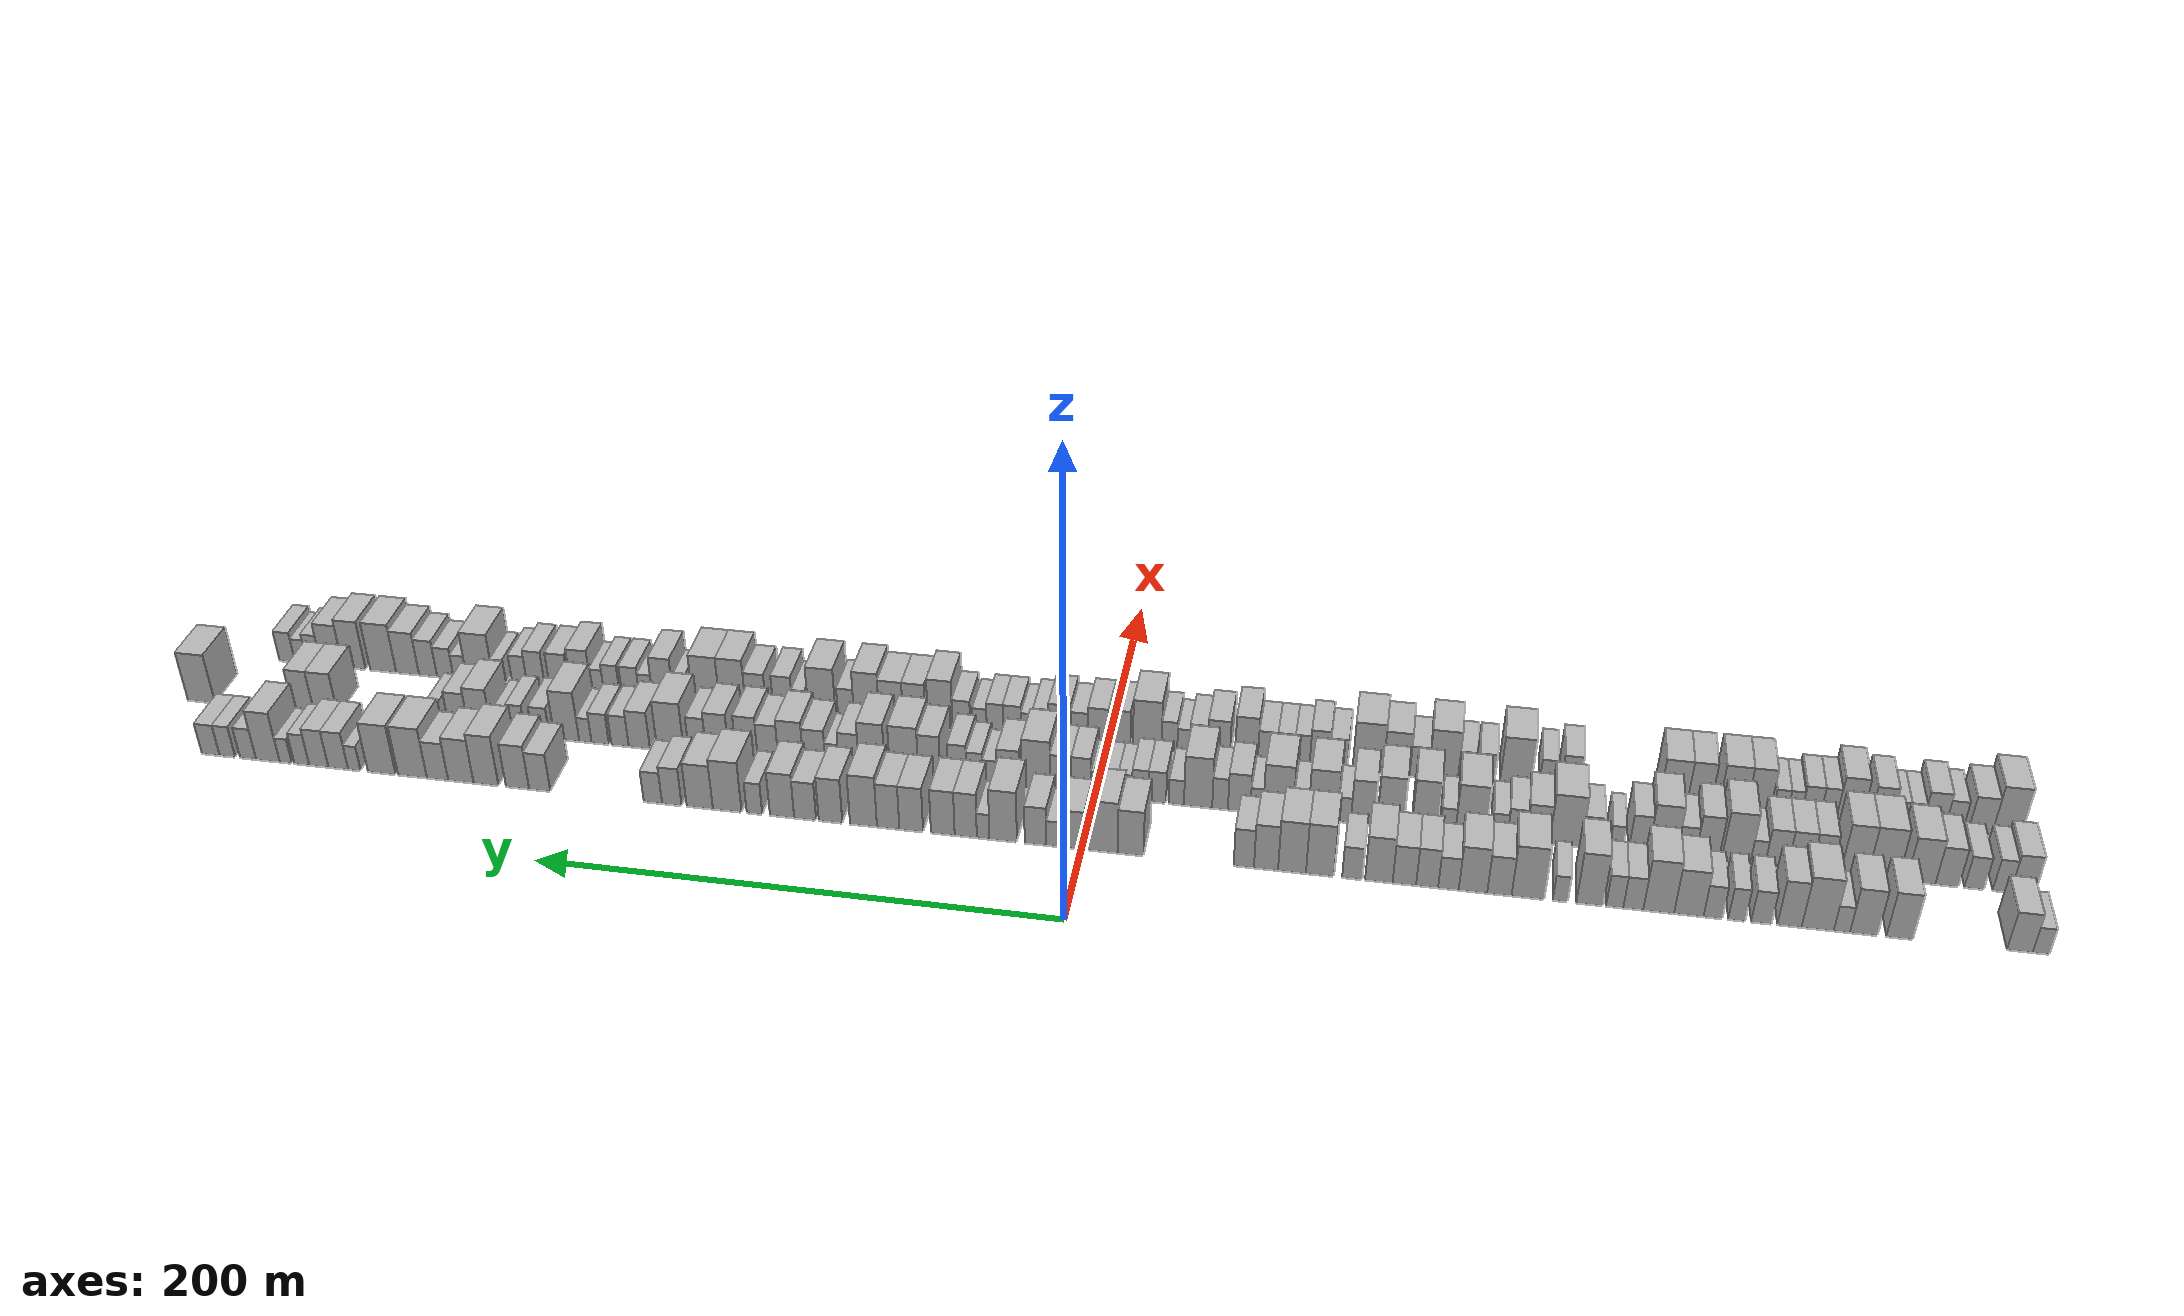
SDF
<sdf version="1.6">
 <world name="default">
  <scene>
   <sky><clouds><speed>12</speed></clouds></sky>
   <ambient>0.4 0.4 0.4 1</ambient>
   <background>0.7 0.7 0.7 1</background>
   <shadows>1</shadows>
  </scene>
  <gravity>0 0 -9.8066</gravity>
  <magnetic_field>6e-06 2.3e-05 -4.2e-05</magnetic_field>
  <physics default="0" name="default_physics" type="ode">
   <ode>
    <solver>
     <type>quick</type>
     <iters>10</iters>
     <sor>1.0</sor>
     <use_dynamic_moi_rescaling>0</use_dynamic_moi_rescaling>
    </solver>
    <constraints>
     <cfm>0</cfm>
     <erp>0.2</erp>
     <contact_max_correcting_vel>100</contact_max_correcting_vel>
     <contact_surface_layer>0.001</contact_surface_layer>
    </constraints>
   </ode>
   <max_step_size>0.004</max_step_size>
   <real_time_factor>1</real_time_factor>
   <real_time_update_rate>250</real_time_update_rate>
  </physics>
  <light name="sun" type="directional">
   <pose>0 0 10 0 0 0</pose>
   <diffuse>0.8 0.8 0.8 1</diffuse>
   <specular>0.2 0.2 0.2 1</specular>
   <attenuation>
    <range>1000</range>
    <constant>0.9</constant>
    <linear>0.01</linear>
    <quadratic>0.001</quadratic>
   </attenuation>
   <direction>-0.5 0.1 -0.9</direction>
  </light>
  <model name="building_1">
   <static>1</static>
   <pose>50.0000 -345.1191 0 0.000000 0.000000 0.000000</pose>
   <link name="link">
    <pose>0 0 6.00 0 0 0</pose>
    <collision name="collision"><geometry><box><size>20.0000 5.7618 12.0000</size></box></geometry></collision>
    <visual name="visual">
     <cast_shadows>0</cast_shadows>
     <geometry><box><size>20.0000 5.7618 12.0000</size></box></geometry>
     <material>
      <script>
       <uri>model://HANNAS_wall/materials/scripts</uri>
       <uri>model://HANNAS_wall/materials/textures</uri>
       <name>vrc/HANNAS_wall</name>
      </script>
     </material>
    </visual>
   </link>
  </model>
  <model name="building_2">
   <static>1</static>
   <pose>50.0000 -337.8096 0 0.000000 0.000000 0.000000</pose>
   <link name="link">
    <pose>0 0 9.00 0 0 0</pose>
    <collision name="collision"><geometry><box><size>20.0000 8.8573 18.0000</size></box></geometry></collision>
    <visual name="visual">
     <cast_shadows>0</cast_shadows>
     <geometry><box><size>20.0000 8.8573 18.0000</size></box></geometry>
     <material>
      <script>
       <uri>model://HANNAS_wall/materials/scripts</uri>
       <uri>model://HANNAS_wall/materials/textures</uri>
       <name>vrc/HANNAS_wall</name>
      </script>
     </material>
    </visual>
   </link>
  </model>
  <model name="building_3">
   <static>1</static>
   <pose>50.0000 -296.4634 0 0.000000 0.000000 0.000000</pose>
   <link name="link">
    <pose>0 0 10.50 0 0 0</pose>
    <collision name="collision"><geometry><box><size>20.0000 9.2784 21.0000</size></box></geometry></collision>
    <visual name="visual">
     <cast_shadows>0</cast_shadows>
     <geometry><box><size>20.0000 9.2784 21.0000</size></box></geometry>
     <material>
      <script>
       <uri>model://HANNAS_wall/materials/scripts</uri>
       <uri>model://HANNAS_wall/materials/textures</uri>
       <name>vrc/HANNAS_wall</name>
      </script>
     </material>
    </visual>
   </link>
  </model>
  <model name="building_4">
   <static>1</static>
   <pose>50.0000 -284.0095 0 0.000000 0.000000 0.000000</pose>
   <link name="link">
    <pose>0 0 10.50 0 0 0</pose>
    <collision name="collision"><geometry><box><size>20.0000 9.6294 21.0000</size></box></geometry></collision>
    <visual name="visual">
     <cast_shadows>0</cast_shadows>
     <geometry><box><size>20.0000 9.6294 21.0000</size></box></geometry>
     <material>
      <script>
       <uri>model://HANNAS_wall/materials/scripts</uri>
       <uri>model://HANNAS_wall/materials/textures</uri>
       <name>vrc/HANNAS_wall</name>
      </script>
     </material>
    </visual>
   </link>
  </model>
  <model name="building_5">
   <static>1</static>
   <pose>50.0000 -276.3685 0 0.000000 0.000000 0.000000</pose>
   <link name="link">
    <pose>0 0 6.00 0 0 0</pose>
    <collision name="collision"><geometry><box><size>20.0000 5.6524 12.0000</size></box></geometry></collision>
    <visual name="visual">
     <cast_shadows>0</cast_shadows>
     <geometry><box><size>20.0000 5.6524 12.0000</size></box></geometry>
     <material>
      <script>
       <uri>model://HANNAS_wall/materials/scripts</uri>
       <uri>model://HANNAS_wall/materials/textures</uri>
       <name>vrc/HANNAS_wall</name>
      </script>
     </material>
    </visual>
   </link>
  </model>
  <model name="building_6">
   <static>1</static>
   <pose>50.0000 -267.9154 0 0.000000 0.000000 0.000000</pose>
   <link name="link">
    <pose>0 0 12.00 0 0 0</pose>
    <collision name="collision"><geometry><box><size>20.0000 11.2537 24.0000</size></box></geometry></collision>
    <visual name="visual">
     <cast_shadows>0</cast_shadows>
     <geometry><box><size>20.0000 11.2537 24.0000</size></box></geometry>
     <material>
      <script>
       <uri>model://HANNAS_wall/materials/scripts</uri>
       <uri>model://HANNAS_wall/materials/textures</uri>
       <name>vrc/HANNAS_wall</name>
      </script>
     </material>
    </visual>
   </link>
  </model>
  <model name="building_7">
   <static>1</static>
   <pose>50.0000 -258.0364 0 0.000000 0.000000 0.000000</pose>
   <link name="link">
    <pose>0 0 10.50 0 0 0</pose>
    <collision name="collision"><geometry><box><size>20.0000 8.5043 21.0000</size></box></geometry></collision>
    <visual name="visual">
     <cast_shadows>0</cast_shadows>
     <geometry><box><size>20.0000 8.5043 21.0000</size></box></geometry>
     <material>
      <script>
       <uri>model://HANNAS_wall/materials/scripts</uri>
       <uri>model://HANNAS_wall/materials/textures</uri>
       <name>vrc/HANNAS_wall</name>
      </script>
     </material>
    </visual>
   </link>
  </model>
  <model name="building_8">
   <static>1</static>
   <pose>50.0000 -248.1728 0 0.000000 0.000000 0.000000</pose>
   <link name="link">
    <pose>0 0 7.50 0 0 0</pose>
    <collision name="collision"><geometry><box><size>20.0000 7.2229 15.0000</size></box></geometry></collision>
    <visual name="visual">
     <cast_shadows>0</cast_shadows>
     <geometry><box><size>20.0000 7.2229 15.0000</size></box></geometry>
     <material>
      <script>
       <uri>model://HANNAS_wall/materials/scripts</uri>
       <uri>model://HANNAS_wall/materials/textures</uri>
       <name>vrc/HANNAS_wall</name>
      </script>
     </material>
    </visual>
   </link>
  </model>
  <model name="building_9">
   <static>1</static>
   <pose>50.0000 -239.5323 0 0.000000 0.000000 0.000000</pose>
   <link name="link">
    <pose>0 0 7.50 0 0 0</pose>
    <collision name="collision"><geometry><box><size>20.0000 6.0581 15.0000</size></box></geometry></collision>
    <visual name="visual">
     <cast_shadows>0</cast_shadows>
     <geometry><box><size>20.0000 6.0581 15.0000</size></box></geometry>
     <material>
      <script>
       <uri>model://HANNAS_wall/materials/scripts</uri>
       <uri>model://HANNAS_wall/materials/textures</uri>
       <name>vrc/HANNAS_wall</name>
      </script>
     </material>
    </visual>
   </link>
  </model>
  <model name="building_10">
   <static>1</static>
   <pose>50.0000 -231.1441 0 0.000000 0.000000 0.000000</pose>
   <link name="link">
    <pose>0 0 7.50 0 0 0</pose>
    <collision name="collision"><geometry><box><size>20.0000 6.7183 15.0000</size></box></geometry></collision>
    <visual name="visual">
     <cast_shadows>0</cast_shadows>
     <geometry><box><size>20.0000 6.7183 15.0000</size></box></geometry>
     <material>
      <script>
       <uri>model://HANNAS_wall/materials/scripts</uri>
       <uri>model://HANNAS_wall/materials/textures</uri>
       <name>vrc/HANNAS_wall</name>
      </script>
     </material>
    </visual>
   </link>
  </model>
  <model name="building_11">
   <static>1</static>
   <pose>50.0000 -222.5589 0 0.000000 0.000000 0.000000</pose>
   <link name="link">
    <pose>0 0 10.50 0 0 0</pose>
    <collision name="collision"><geometry><box><size>20.0000 10.4522 21.0000</size></box></geometry></collision>
    <visual name="visual">
     <cast_shadows>0</cast_shadows>
     <geometry><box><size>20.0000 10.4522 21.0000</size></box></geometry>
     <material>
      <script>
       <uri>model://HANNAS_wall/materials/scripts</uri>
       <uri>model://HANNAS_wall/materials/textures</uri>
       <name>vrc/HANNAS_wall</name>
      </script>
     </material>
    </visual>
   </link>
  </model>
  <model name="building_12">
   <static>1</static>
   <pose>50.0000 -211.8598 0 0.000000 0.000000 0.000000</pose>
   <link name="link">
    <pose>0 0 12.00 0 0 0</pose>
    <collision name="collision"><geometry><box><size>20.0000 10.9460 24.0000</size></box></geometry></collision>
    <visual name="visual">
     <cast_shadows>0</cast_shadows>
     <geometry><box><size>20.0000 10.9460 24.0000</size></box></geometry>
     <material>
      <script>
       <uri>model://HANNAS_wall/materials/scripts</uri>
       <uri>model://HANNAS_wall/materials/textures</uri>
       <name>vrc/HANNAS_wall</name>
      </script>
     </material>
    </visual>
   </link>
  </model>
  <model name="building_13">
   <static>1</static>
   <pose>50.0000 -202.8306 0 0.000000 0.000000 0.000000</pose>
   <link name="link">
    <pose>0 0 7.50 0 0 0</pose>
    <collision name="collision"><geometry><box><size>20.0000 7.1125 15.0000</size></box></geometry></collision>
    <visual name="visual">
     <cast_shadows>0</cast_shadows>
     <geometry><box><size>20.0000 7.1125 15.0000</size></box></geometry>
     <material>
      <script>
       <uri>model://HANNAS_wall/materials/scripts</uri>
       <uri>model://HANNAS_wall/materials/textures</uri>
       <name>vrc/HANNAS_wall</name>
      </script>
     </material>
    </visual>
   </link>
  </model>
  <model name="building_14">
   <static>1</static>
   <pose>50.0000 -196.1924 0 0.000000 0.000000 0.000000</pose>
   <link name="link">
    <pose>0 0 7.50 0 0 0</pose>
    <collision name="collision"><geometry><box><size>20.0000 6.1640 15.0000</size></box></geometry></collision>
    <visual name="visual">
     <cast_shadows>0</cast_shadows>
     <geometry><box><size>20.0000 6.1640 15.0000</size></box></geometry>
     <material>
      <script>
       <uri>model://HANNAS_wall/materials/scripts</uri>
       <uri>model://HANNAS_wall/materials/textures</uri>
       <name>vrc/HANNAS_wall</name>
      </script>
     </material>
    </visual>
   </link>
  </model>
  <model name="building_15">
   <static>1</static>
   <pose>50.0000 -187.2749 0 0.000000 0.000000 0.000000</pose>
   <link name="link">
    <pose>0 0 12.00 0 0 0</pose>
    <collision name="collision"><geometry><box><size>20.0000 9.6709 24.0000</size></box></geometry></collision>
    <visual name="visual">
     <cast_shadows>0</cast_shadows>
     <geometry><box><size>20.0000 9.6709 24.0000</size></box></geometry>
     <material>
      <script>
       <uri>model://HANNAS_wall/materials/scripts</uri>
       <uri>model://HANNAS_wall/materials/textures</uri>
       <name>vrc/HANNAS_wall</name>
      </script>
     </material>
    </visual>
   </link>
  </model>
  <model name="building_16">
   <static>1</static>
   <pose>50.0000 -176.7070 0 0.000000 0.000000 0.000000</pose>
   <link name="link">
    <pose>0 0 6.00 0 0 0</pose>
    <collision name="collision"><geometry><box><size>20.0000 5.4650 12.0000</size></box></geometry></collision>
    <visual name="visual">
     <cast_shadows>0</cast_shadows>
     <geometry><box><size>20.0000 5.4650 12.0000</size></box></geometry>
     <material>
      <script>
       <uri>model://HANNAS_wall/materials/scripts</uri>
       <uri>model://HANNAS_wall/materials/textures</uri>
       <name>vrc/HANNAS_wall</name>
      </script>
     </material>
    </visual>
   </link>
  </model>
  <model name="building_17">
   <static>1</static>
   <pose>50.0000 -165.0392 0 0.000000 0.000000 0.000000</pose>
   <link name="link">
    <pose>0 0 12.00 0 0 0</pose>
    <collision name="collision"><geometry><box><size>20.0000 11.8706 24.0000</size></box></geometry></collision>
    <visual name="visual">
     <cast_shadows>0</cast_shadows>
     <geometry><box><size>20.0000 11.8706 24.0000</size></box></geometry>
     <material>
      <script>
       <uri>model://HANNAS_wall/materials/scripts</uri>
       <uri>model://HANNAS_wall/materials/textures</uri>
       <name>vrc/HANNAS_wall</name>
      </script>
     </material>
    </visual>
   </link>
  </model>
  <model name="building_18">
   <static>1</static>
   <pose>50.0000 -154.6894 0 0.000000 0.000000 0.000000</pose>
   <link name="link">
    <pose>0 0 9.00 0 0 0</pose>
    <collision name="collision"><geometry><box><size>20.0000 8.8291 18.0000</size></box></geometry></collision>
    <visual name="visual">
     <cast_shadows>0</cast_shadows>
     <geometry><box><size>20.0000 8.8291 18.0000</size></box></geometry>
     <material>
      <script>
       <uri>model://HANNAS_wall/materials/scripts</uri>
       <uri>model://HANNAS_wall/materials/textures</uri>
       <name>vrc/HANNAS_wall</name>
      </script>
     </material>
    </visual>
   </link>
  </model>
  <model name="building_19">
   <static>1</static>
   <pose>50.0000 -145.1029 0 0.000000 0.000000 0.000000</pose>
   <link name="link">
    <pose>0 0 10.50 0 0 0</pose>
    <collision name="collision"><geometry><box><size>20.0000 10.3438 21.0000</size></box></geometry></collision>
    <visual name="visual">
     <cast_shadows>0</cast_shadows>
     <geometry><box><size>20.0000 10.3438 21.0000</size></box></geometry>
     <material>
      <script>
       <uri>model://HANNAS_wall/materials/scripts</uri>
       <uri>model://HANNAS_wall/materials/textures</uri>
       <name>vrc/HANNAS_wall</name>
      </script>
     </material>
    </visual>
   </link>
  </model>
  <model name="building_20">
   <static>1</static>
   <pose>50.0000 -136.1869 0 0.000000 0.000000 0.000000</pose>
   <link name="link">
    <pose>0 0 7.50 0 0 0</pose>
    <collision name="collision"><geometry><box><size>20.0000 7.4882 15.0000</size></box></geometry></collision>
    <visual name="visual">
     <cast_shadows>0</cast_shadows>
     <geometry><box><size>20.0000 7.4882 15.0000</size></box></geometry>
     <material>
      <script>
       <uri>model://HANNAS_wall/materials/scripts</uri>
       <uri>model://HANNAS_wall/materials/textures</uri>
       <name>vrc/HANNAS_wall</name>
      </script>
     </material>
    </visual>
   </link>
  </model>
  <model name="building_21">
   <static>1</static>
   <pose>50.0000 -128.4151 0 0.000000 0.000000 0.000000</pose>
   <link name="link">
    <pose>0 0 9.00 0 0 0</pose>
    <collision name="collision"><geometry><box><size>20.0000 8.0554 18.0000</size></box></geometry></collision>
    <visual name="visual">
     <cast_shadows>0</cast_shadows>
     <geometry><box><size>20.0000 8.0554 18.0000</size></box></geometry>
     <material>
      <script>
       <uri>model://HANNAS_wall/materials/scripts</uri>
       <uri>model://HANNAS_wall/materials/textures</uri>
       <name>vrc/HANNAS_wall</name>
      </script>
     </material>
    </visual>
   </link>
  </model>
  <model name="building_22">
   <static>1</static>
   <pose>50.0000 -120.0876 0 0.000000 0.000000 0.000000</pose>
   <link name="link">
    <pose>0 0 9.00 0 0 0</pose>
    <collision name="collision"><geometry><box><size>20.0000 8.5995 18.0000</size></box></geometry></collision>
    <visual name="visual">
     <cast_shadows>0</cast_shadows>
     <geometry><box><size>20.0000 8.5995 18.0000</size></box></geometry>
     <material>
      <script>
       <uri>model://HANNAS_wall/materials/scripts</uri>
       <uri>model://HANNAS_wall/materials/textures</uri>
       <name>vrc/HANNAS_wall</name>
      </script>
     </material>
    </visual>
   </link>
  </model>
  <model name="building_23">
   <static>1</static>
   <pose>50.0000 -110.7468 0 0.000000 0.000000 0.000000</pose>
   <link name="link">
    <pose>0 0 10.50 0 0 0</pose>
    <collision name="collision"><geometry><box><size>20.0000 10.0822 21.0000</size></box></geometry></collision>
    <visual name="visual">
     <cast_shadows>0</cast_shadows>
     <geometry><box><size>20.0000 10.0822 21.0000</size></box></geometry>
     <material>
      <script>
       <uri>model://HANNAS_wall/materials/scripts</uri>
       <uri>model://HANNAS_wall/materials/textures</uri>
       <name>vrc/HANNAS_wall</name>
      </script>
     </material>
    </visual>
   </link>
  </model>
  <model name="building_24">
   <static>1</static>
   <pose>50.0000 -100.9784 0 0.000000 0.000000 0.000000</pose>
   <link name="link">
    <pose>0 0 7.50 0 0 0</pose>
    <collision name="collision"><geometry><box><size>20.0000 7.4545 15.0000</size></box></geometry></collision>
    <visual name="visual">
     <cast_shadows>0</cast_shadows>
     <geometry><box><size>20.0000 7.4545 15.0000</size></box></geometry>
     <material>
      <script>
       <uri>model://HANNAS_wall/materials/scripts</uri>
       <uri>model://HANNAS_wall/materials/textures</uri>
       <name>vrc/HANNAS_wall</name>
      </script>
     </material>
    </visual>
   </link>
  </model>
  <model name="building_25">
   <static>1</static>
   <pose>50.0000 -89.0667 0 0.000000 0.000000 0.000000</pose>
   <link name="link">
    <pose>0 0 12.00 0 0 0</pose>
    <collision name="collision"><geometry><box><size>20.0000 10.3689 24.0000</size></box></geometry></collision>
    <visual name="visual">
     <cast_shadows>0</cast_shadows>
     <geometry><box><size>20.0000 10.3689 24.0000</size></box></geometry>
     <material>
      <script>
       <uri>model://HANNAS_wall/materials/scripts</uri>
       <uri>model://HANNAS_wall/materials/textures</uri>
       <name>vrc/HANNAS_wall</name>
      </script>
     </material>
    </visual>
   </link>
  </model>
  <model name="building_26">
   <static>1</static>
   <pose>50.0000 -78.7069 0 0.000000 0.000000 0.000000</pose>
   <link name="link">
    <pose>0 0 12.00 0 0 0</pose>
    <collision name="collision"><geometry><box><size>20.0000 10.3507 24.0000</size></box></geometry></collision>
    <visual name="visual">
     <cast_shadows>0</cast_shadows>
     <geometry><box><size>20.0000 10.3507 24.0000</size></box></geometry>
     <material>
      <script>
       <uri>model://HANNAS_wall/materials/scripts</uri>
       <uri>model://HANNAS_wall/materials/textures</uri>
       <name>vrc/HANNAS_wall</name>
      </script>
     </material>
    </visual>
   </link>
  </model>
  <model name="building_27">
   <static>1</static>
   <pose>50.0000 -69.0423 0 0.000000 0.000000 0.000000</pose>
   <link name="link">
    <pose>0 0 10.50 0 0 0</pose>
    <collision name="collision"><geometry><box><size>20.0000 8.9786 21.0000</size></box></geometry></collision>
    <visual name="visual">
     <cast_shadows>0</cast_shadows>
     <geometry><box><size>20.0000 8.9786 21.0000</size></box></geometry>
     <material>
      <script>
       <uri>model://HANNAS_wall/materials/scripts</uri>
       <uri>model://HANNAS_wall/materials/textures</uri>
       <name>vrc/HANNAS_wall</name>
      </script>
     </material>
    </visual>
   </link>
  </model>
  <model name="building_28">
   <static>1</static>
   <pose>50.0000 -60.7804 0 0.000000 0.000000 0.000000</pose>
   <link name="link">
    <pose>0 0 9.00 0 0 0</pose>
    <collision name="collision"><geometry><box><size>20.0000 7.5452 18.0000</size></box></geometry></collision>
    <visual name="visual">
     <cast_shadows>0</cast_shadows>
     <geometry><box><size>20.0000 7.5452 18.0000</size></box></geometry>
     <material>
      <script>
       <uri>model://HANNAS_wall/materials/scripts</uri>
       <uri>model://HANNAS_wall/materials/textures</uri>
       <name>vrc/HANNAS_wall</name>
      </script>
     </material>
    </visual>
   </link>
  </model>
  <model name="building_29">
   <static>1</static>
   <pose>50.0000 -18.3512 0 0.000000 0.000000 0.000000</pose>
   <link name="link">
    <pose>0 0 10.50 0 0 0</pose>
    <collision name="collision"><geometry><box><size>20.0000 9.7710 21.0000</size></box></geometry></collision>
    <visual name="visual">
     <cast_shadows>0</cast_shadows>
     <geometry><box><size>20.0000 9.7710 21.0000</size></box></geometry>
     <material>
      <script>
       <uri>model://HANNAS_wall/materials/scripts</uri>
       <uri>model://HANNAS_wall/materials/textures</uri>
       <name>vrc/HANNAS_wall</name>
      </script>
     </material>
    </visual>
   </link>
  </model>
  <model name="building_30">
   <static>1</static>
   <pose>50.0000 -7.5847 0 0.000000 0.000000 0.000000</pose>
   <link name="link">
    <pose>0 0 12.00 0 0 0</pose>
    <collision name="collision"><geometry><box><size>20.0000 11.7621 24.0000</size></box></geometry></collision>
    <visual name="visual">
     <cast_shadows>0</cast_shadows>
     <geometry><box><size>20.0000 11.7621 24.0000</size></box></geometry>
     <material>
      <script>
       <uri>model://HANNAS_wall/materials/scripts</uri>
       <uri>model://HANNAS_wall/materials/textures</uri>
       <name>vrc/HANNAS_wall</name>
      </script>
     </material>
    </visual>
   </link>
  </model>
  <model name="building_31">
   <static>1</static>
   <pose>50.0000 3.7757 0 0.000000 0.000000 0.000000</pose>
   <link name="link">
    <pose>0 0 9.00 0 0 0</pose>
    <collision name="collision"><geometry><box><size>20.0000 8.9586 18.0000</size></box></geometry></collision>
    <visual name="visual">
     <cast_shadows>0</cast_shadows>
     <geometry><box><size>20.0000 8.9586 18.0000</size></box></geometry>
     <material>
      <script>
       <uri>model://HANNAS_wall/materials/scripts</uri>
       <uri>model://HANNAS_wall/materials/textures</uri>
       <name>vrc/HANNAS_wall</name>
      </script>
     </material>
    </visual>
   </link>
  </model>
  <model name="building_32">
   <static>1</static>
   <pose>50.0000 10.9654 0 0.000000 0.000000 0.000000</pose>
   <link name="link">
    <pose>0 0 6.00 0 0 0</pose>
    <collision name="collision"><geometry><box><size>20.0000 5.4208 12.0000</size></box></geometry></collision>
    <visual name="visual">
     <cast_shadows>0</cast_shadows>
     <geometry><box><size>20.0000 5.4208 12.0000</size></box></geometry>
     <material>
      <script>
       <uri>model://HANNAS_wall/materials/scripts</uri>
       <uri>model://HANNAS_wall/materials/textures</uri>
       <name>vrc/HANNAS_wall</name>
      </script>
     </material>
    </visual>
   </link>
  </model>
  <model name="building_33">
   <static>1</static>
   <pose>50.0000 17.8217 0 0.000000 0.000000 0.000000</pose>
   <link name="link">
    <pose>0 0 9.00 0 0 0</pose>
    <collision name="collision"><geometry><box><size>20.0000 8.2917 18.0000</size></box></geometry></collision>
    <visual name="visual">
     <cast_shadows>0</cast_shadows>
     <geometry><box><size>20.0000 8.2917 18.0000</size></box></geometry>
     <material>
      <script>
       <uri>model://HANNAS_wall/materials/scripts</uri>
       <uri>model://HANNAS_wall/materials/textures</uri>
       <name>vrc/HANNAS_wall</name>
      </script>
     </material>
    </visual>
   </link>
  </model>
  <model name="building_34">
   <static>1</static>
   <pose>50.0000 30.2291 0 0.000000 0.000000 0.000000</pose>
   <link name="link">
    <pose>0 0 12.00 0 0 0</pose>
    <collision name="collision"><geometry><box><size>20.0000 10.5231 24.0000</size></box></geometry></collision>
    <visual name="visual">
     <cast_shadows>0</cast_shadows>
     <geometry><box><size>20.0000 10.5231 24.0000</size></box></geometry>
     <material>
      <script>
       <uri>model://HANNAS_wall/materials/scripts</uri>
       <uri>model://HANNAS_wall/materials/textures</uri>
       <name>vrc/HANNAS_wall</name>
      </script>
     </material>
    </visual>
   </link>
  </model>
  <model name="building_35">
   <static>1</static>
   <pose>50.0000 37.9034 0 0.000000 0.000000 0.000000</pose>
   <link name="link">
    <pose>0 0 6.00 0 0 0</pose>
    <collision name="collision"><geometry><box><size>20.0000 4.8255 12.0000</size></box></geometry></collision>
    <visual name="visual">
     <cast_shadows>0</cast_shadows>
     <geometry><box><size>20.0000 4.8255 12.0000</size></box></geometry>
     <material>
      <script>
       <uri>model://HANNAS_wall/materials/scripts</uri>
       <uri>model://HANNAS_wall/materials/textures</uri>
       <name>vrc/HANNAS_wall</name>
      </script>
     </material>
    </visual>
   </link>
  </model>
  <model name="building_36">
   <static>1</static>
   <pose>50.0000 44.5834 0 0.000000 0.000000 0.000000</pose>
   <link name="link">
    <pose>0 0 10.50 0 0 0</pose>
    <collision name="collision"><geometry><box><size>20.0000 8.5345 21.0000</size></box></geometry></collision>
    <visual name="visual">
     <cast_shadows>0</cast_shadows>
     <geometry><box><size>20.0000 8.5345 21.0000</size></box></geometry>
     <material>
      <script>
       <uri>model://HANNAS_wall/materials/scripts</uri>
       <uri>model://HANNAS_wall/materials/textures</uri>
       <name>vrc/HANNAS_wall</name>
      </script>
     </material>
    </visual>
   </link>
  </model>
  <model name="building_37">
   <static>1</static>
   <pose>50.0000 53.4414 0 0.000000 0.000000 0.000000</pose>
   <link name="link">
    <pose>0 0 10.50 0 0 0</pose>
    <collision name="collision"><geometry><box><size>20.0000 9.1814 21.0000</size></box></geometry></collision>
    <visual name="visual">
     <cast_shadows>0</cast_shadows>
     <geometry><box><size>20.0000 9.1814 21.0000</size></box></geometry>
     <material>
      <script>
       <uri>model://HANNAS_wall/materials/scripts</uri>
       <uri>model://HANNAS_wall/materials/textures</uri>
       <name>vrc/HANNAS_wall</name>
      </script>
     </material>
    </visual>
   </link>
  </model>
  <model name="building_38">
   <static>1</static>
   <pose>50.0000 65.6423 0 0.000000 0.000000 0.000000</pose>
   <link name="link">
    <pose>0 0 10.50 0 0 0</pose>
    <collision name="collision"><geometry><box><size>20.0000 9.2204 21.0000</size></box></geometry></collision>
    <visual name="visual">
     <cast_shadows>0</cast_shadows>
     <geometry><box><size>20.0000 9.2204 21.0000</size></box></geometry>
     <material>
      <script>
       <uri>model://HANNAS_wall/materials/scripts</uri>
       <uri>model://HANNAS_wall/materials/textures</uri>
       <name>vrc/HANNAS_wall</name>
      </script>
     </material>
    </visual>
   </link>
  </model>
  <model name="building_39">
   <static>1</static>
   <pose>50.0000 74.6010 0 0.000000 0.000000 0.000000</pose>
   <link name="link">
    <pose>0 0 10.50 0 0 0</pose>
    <collision name="collision"><geometry><box><size>20.0000 8.6968 21.0000</size></box></geometry></collision>
    <visual name="visual">
     <cast_shadows>0</cast_shadows>
     <geometry><box><size>20.0000 8.6968 21.0000</size></box></geometry>
     <material>
      <script>
       <uri>model://HANNAS_wall/materials/scripts</uri>
       <uri>model://HANNAS_wall/materials/textures</uri>
       <name>vrc/HANNAS_wall</name>
      </script>
     </material>
    </visual>
   </link>
  </model>
  <model name="building_40">
   <static>1</static>
   <pose>50.0000 84.2003 0 0.000000 0.000000 0.000000</pose>
   <link name="link">
    <pose>0 0 12.00 0 0 0</pose>
    <collision name="collision"><geometry><box><size>20.0000 10.5019 24.0000</size></box></geometry></collision>
    <visual name="visual">
     <cast_shadows>0</cast_shadows>
     <geometry><box><size>20.0000 10.5019 24.0000</size></box></geometry>
     <material>
      <script>
       <uri>model://HANNAS_wall/materials/scripts</uri>
       <uri>model://HANNAS_wall/materials/textures</uri>
       <name>vrc/HANNAS_wall</name>
      </script>
     </material>
    </visual>
   </link>
  </model>
  <model name="building_41">
   <static>1</static>
   <pose>50.0000 97.0796 0 0.000000 0.000000 0.000000</pose>
   <link name="link">
    <pose>0 0 10.50 0 0 0</pose>
    <collision name="collision"><geometry><box><size>20.0000 9.2566 21.0000</size></box></geometry></collision>
    <visual name="visual">
     <cast_shadows>0</cast_shadows>
     <geometry><box><size>20.0000 9.2566 21.0000</size></box></geometry>
     <material>
      <script>
       <uri>model://HANNAS_wall/materials/scripts</uri>
       <uri>model://HANNAS_wall/materials/textures</uri>
       <name>vrc/HANNAS_wall</name>
      </script>
     </material>
    </visual>
   </link>
  </model>
  <model name="building_42">
   <static>1</static>
   <pose>50.0000 107.0255 0 0.000000 0.000000 0.000000</pose>
   <link name="link">
    <pose>0 0 9.00 0 0 0</pose>
    <collision name="collision"><geometry><box><size>20.0000 8.6352 18.0000</size></box></geometry></collision>
    <visual name="visual">
     <cast_shadows>0</cast_shadows>
     <geometry><box><size>20.0000 8.6352 18.0000</size></box></geometry>
     <material>
      <script>
       <uri>model://HANNAS_wall/materials/scripts</uri>
       <uri>model://HANNAS_wall/materials/textures</uri>
       <name>vrc/HANNAS_wall</name>
      </script>
     </material>
    </visual>
   </link>
  </model>
  <model name="building_43">
   <static>1</static>
   <pose>50.0000 116.1089 0 0.000000 0.000000 0.000000</pose>
   <link name="link">
    <pose>0 0 10.50 0 0 0</pose>
    <collision name="collision"><geometry><box><size>20.0000 9.5316 21.0000</size></box></geometry></collision>
    <visual name="visual">
     <cast_shadows>0</cast_shadows>
     <geometry><box><size>20.0000 9.5316 21.0000</size></box></geometry>
     <material>
      <script>
       <uri>model://HANNAS_wall/materials/scripts</uri>
       <uri>model://HANNAS_wall/materials/textures</uri>
       <name>vrc/HANNAS_wall</name>
      </script>
     </material>
    </visual>
   </link>
  </model>
  <model name="building_44">
   <static>1</static>
   <pose>50.0000 126.9574 0 0.000000 0.000000 0.000000</pose>
   <link name="link">
    <pose>0 0 7.50 0 0 0</pose>
    <collision name="collision"><geometry><box><size>20.0000 6.1653 15.0000</size></box></geometry></collision>
    <visual name="visual">
     <cast_shadows>0</cast_shadows>
     <geometry><box><size>20.0000 6.1653 15.0000</size></box></geometry>
     <material>
      <script>
       <uri>model://HANNAS_wall/materials/scripts</uri>
       <uri>model://HANNAS_wall/materials/textures</uri>
       <name>vrc/HANNAS_wall</name>
      </script>
     </material>
    </visual>
   </link>
  </model>
  <model name="building_45">
   <static>1</static>
   <pose>50.0000 137.7433 0 0.000000 0.000000 0.000000</pose>
   <link name="link">
    <pose>0 0 12.00 0 0 0</pose>
    <collision name="collision"><geometry><box><size>20.0000 11.4064 24.0000</size></box></geometry></collision>
    <visual name="visual">
     <cast_shadows>0</cast_shadows>
     <geometry><box><size>20.0000 11.4064 24.0000</size></box></geometry>
     <material>
      <script>
       <uri>model://HANNAS_wall/materials/scripts</uri>
       <uri>model://HANNAS_wall/materials/textures</uri>
       <name>vrc/HANNAS_wall</name>
      </script>
     </material>
    </visual>
   </link>
  </model>
  <model name="building_46">
   <static>1</static>
   <pose>50.0000 148.6436 0 0.000000 0.000000 0.000000</pose>
   <link name="link">
    <pose>0 0 10.50 0 0 0</pose>
    <collision name="collision"><geometry><box><size>20.0000 10.3942 21.0000</size></box></geometry></collision>
    <visual name="visual">
     <cast_shadows>0</cast_shadows>
     <geometry><box><size>20.0000 10.3942 21.0000</size></box></geometry>
     <material>
      <script>
       <uri>model://HANNAS_wall/materials/scripts</uri>
       <uri>model://HANNAS_wall/materials/textures</uri>
       <name>vrc/HANNAS_wall</name>
      </script>
     </material>
    </visual>
   </link>
  </model>
  <model name="building_47">
   <static>1</static>
   <pose>50.0000 159.7415 0 0.000000 0.000000 0.000000</pose>
   <link name="link">
    <pose>0 0 9.00 0 0 0</pose>
    <collision name="collision"><geometry><box><size>20.0000 7.8018 18.0000</size></box></geometry></collision>
    <visual name="visual">
     <cast_shadows>0</cast_shadows>
     <geometry><box><size>20.0000 7.8018 18.0000</size></box></geometry>
     <material>
      <script>
       <uri>model://HANNAS_wall/materials/scripts</uri>
       <uri>model://HANNAS_wall/materials/textures</uri>
       <name>vrc/HANNAS_wall</name>
      </script>
     </material>
    </visual>
   </link>
  </model>
  <model name="building_48">
   <static>1</static>
   <pose>50.0000 167.3226 0 0.000000 0.000000 0.000000</pose>
   <link name="link">
    <pose>0 0 7.50 0 0 0</pose>
    <collision name="collision"><geometry><box><size>20.0000 7.3603 15.0000</size></box></geometry></collision>
    <visual name="visual">
     <cast_shadows>0</cast_shadows>
     <geometry><box><size>20.0000 7.3603 15.0000</size></box></geometry>
     <material>
      <script>
       <uri>model://HANNAS_wall/materials/scripts</uri>
       <uri>model://HANNAS_wall/materials/textures</uri>
       <name>vrc/HANNAS_wall</name>
      </script>
     </material>
    </visual>
   </link>
  </model>
  <model name="building_49">
   <static>1</static>
   <pose>50.0000 212.8651 0 0.000000 0.000000 0.000000</pose>
   <link name="link">
    <pose>0 0 9.00 0 0 0</pose>
    <collision name="collision"><geometry><box><size>20.0000 8.5749 18.0000</size></box></geometry></collision>
    <visual name="visual">
     <cast_shadows>0</cast_shadows>
     <geometry><box><size>20.0000 8.5749 18.0000</size></box></geometry>
     <material>
      <script>
       <uri>model://HANNAS_wall/materials/scripts</uri>
       <uri>model://HANNAS_wall/materials/textures</uri>
       <name>vrc/HANNAS_wall</name>
      </script>
     </material>
    </visual>
   </link>
  </model>
  <model name="building_50">
   <static>1</static>
   <pose>50.0000 221.8781 0 0.000000 0.000000 0.000000</pose>
   <link name="link">
    <pose>0 0 10.50 0 0 0</pose>
    <collision name="collision"><geometry><box><size>20.0000 9.4511 21.0000</size></box></geometry></collision>
    <visual name="visual">
     <cast_shadows>0</cast_shadows>
     <geometry><box><size>20.0000 9.4511 21.0000</size></box></geometry>
     <material>
      <script>
       <uri>model://HANNAS_wall/materials/scripts</uri>
       <uri>model://HANNAS_wall/materials/textures</uri>
       <name>vrc/HANNAS_wall</name>
      </script>
     </material>
    </visual>
   </link>
  </model>
  <model name="building_51">
   <static>1</static>
   <pose>50.0000 234.6874 0 0.000000 0.000000 0.000000</pose>
   <link name="link">
    <pose>0 0 12.00 0 0 0</pose>
    <collision name="collision"><geometry><box><size>20.0000 10.1676 24.0000</size></box></geometry></collision>
    <visual name="visual">
     <cast_shadows>0</cast_shadows>
     <geometry><box><size>20.0000 10.1676 24.0000</size></box></geometry>
     <material>
      <script>
       <uri>model://HANNAS_wall/materials/scripts</uri>
       <uri>model://HANNAS_wall/materials/textures</uri>
       <name>vrc/HANNAS_wall</name>
      </script>
     </material>
    </visual>
   </link>
  </model>
  <model name="building_52">
   <static>1</static>
   <pose>50.0000 244.9730 0 0.000000 0.000000 0.000000</pose>
   <link name="link">
    <pose>0 0 10.50 0 0 0</pose>
    <collision name="collision"><geometry><box><size>20.0000 10.4035 21.0000</size></box></geometry></collision>
    <visual name="visual">
     <cast_shadows>0</cast_shadows>
     <geometry><box><size>20.0000 10.4035 21.0000</size></box></geometry>
     <material>
      <script>
       <uri>model://HANNAS_wall/materials/scripts</uri>
       <uri>model://HANNAS_wall/materials/textures</uri>
       <name>vrc/HANNAS_wall</name>
      </script>
     </material>
    </visual>
   </link>
  </model>
  <model name="building_53">
   <static>1</static>
   <pose>50.0000 254.5338 0 0.000000 0.000000 0.000000</pose>
   <link name="link">
    <pose>0 0 9.00 0 0 0</pose>
    <collision name="collision"><geometry><box><size>20.0000 8.7182 18.0000</size></box></geometry></collision>
    <visual name="visual">
     <cast_shadows>0</cast_shadows>
     <geometry><box><size>20.0000 8.7182 18.0000</size></box></geometry>
     <material>
      <script>
       <uri>model://HANNAS_wall/materials/scripts</uri>
       <uri>model://HANNAS_wall/materials/textures</uri>
       <name>vrc/HANNAS_wall</name>
      </script>
     </material>
    </visual>
   </link>
  </model>
  <model name="building_54">
   <static>1</static>
   <pose>50.0000 264.8373 0 0.000000 0.000000 0.000000</pose>
   <link name="link">
    <pose>0 0 12.00 0 0 0</pose>
    <collision name="collision"><geometry><box><size>20.0000 11.8889 24.0000</size></box></geometry></collision>
    <visual name="visual">
     <cast_shadows>0</cast_shadows>
     <geometry><box><size>20.0000 11.8889 24.0000</size></box></geometry>
     <material>
      <script>
       <uri>model://HANNAS_wall/materials/scripts</uri>
       <uri>model://HANNAS_wall/materials/textures</uri>
       <name>vrc/HANNAS_wall</name>
      </script>
     </material>
    </visual>
   </link>
  </model>
  <model name="building_55">
   <static>1</static>
   <pose>50.0000 277.5243 0 0.000000 0.000000 0.000000</pose>
   <link name="link">
    <pose>0 0 12.00 0 0 0</pose>
    <collision name="collision"><geometry><box><size>20.0000 11.4850 24.0000</size></box></geometry></collision>
    <visual name="visual">
     <cast_shadows>0</cast_shadows>
     <geometry><box><size>20.0000 11.4850 24.0000</size></box></geometry>
     <material>
      <script>
       <uri>model://HANNAS_wall/materials/scripts</uri>
       <uri>model://HANNAS_wall/materials/textures</uri>
       <name>vrc/HANNAS_wall</name>
      </script>
     </material>
    </visual>
   </link>
  </model>
  <model name="building_56">
   <static>1</static>
   <pose>50.0000 288.8443 0 0.000000 0.000000 0.000000</pose>
   <link name="link">
    <pose>0 0 6.00 0 0 0</pose>
    <collision name="collision"><geometry><box><size>20.0000 5.1550 12.0000</size></box></geometry></collision>
    <visual name="visual">
     <cast_shadows>0</cast_shadows>
     <geometry><box><size>20.0000 5.1550 12.0000</size></box></geometry>
     <material>
      <script>
       <uri>model://HANNAS_wall/materials/scripts</uri>
       <uri>model://HANNAS_wall/materials/textures</uri>
       <name>vrc/HANNAS_wall</name>
      </script>
     </material>
    </visual>
   </link>
  </model>
  <model name="building_57">
   <static>1</static>
   <pose>50.0000 295.5241 0 0.000000 0.000000 0.000000</pose>
   <link name="link">
    <pose>0 0 9.00 0 0 0</pose>
    <collision name="collision"><geometry><box><size>20.0000 8.2046 18.0000</size></box></geometry></collision>
    <visual name="visual">
     <cast_shadows>0</cast_shadows>
     <geometry><box><size>20.0000 8.2046 18.0000</size></box></geometry>
     <material>
      <script>
       <uri>model://HANNAS_wall/materials/scripts</uri>
       <uri>model://HANNAS_wall/materials/textures</uri>
       <name>vrc/HANNAS_wall</name>
      </script>
     </material>
    </visual>
   </link>
  </model>
  <model name="building_58">
   <static>1</static>
   <pose>50.0000 303.6294 0 0.000000 0.000000 0.000000</pose>
   <link name="link">
    <pose>0 0 9.00 0 0 0</pose>
    <collision name="collision"><geometry><box><size>20.0000 8.0060 18.0000</size></box></geometry></collision>
    <visual name="visual">
     <cast_shadows>0</cast_shadows>
     <geometry><box><size>20.0000 8.0060 18.0000</size></box></geometry>
     <material>
      <script>
       <uri>model://HANNAS_wall/materials/scripts</uri>
       <uri>model://HANNAS_wall/materials/textures</uri>
       <name>vrc/HANNAS_wall</name>
      </script>
     </material>
    </visual>
   </link>
  </model>
  <model name="building_59">
   <static>1</static>
   <pose>50.0000 310.7290 0 0.000000 0.000000 0.000000</pose>
   <link name="link">
    <pose>0 0 7.50 0 0 0</pose>
    <collision name="collision"><geometry><box><size>20.0000 6.1931 15.0000</size></box></geometry></collision>
    <visual name="visual">
     <cast_shadows>0</cast_shadows>
     <geometry><box><size>20.0000 6.1931 15.0000</size></box></geometry>
     <material>
      <script>
       <uri>model://HANNAS_wall/materials/scripts</uri>
       <uri>model://HANNAS_wall/materials/textures</uri>
       <name>vrc/HANNAS_wall</name>
      </script>
     </material>
    </visual>
   </link>
  </model>
  <model name="building_60">
   <static>1</static>
   <pose>50.0000 317.3762 0 0.000000 0.000000 0.000000</pose>
   <link name="link">
    <pose>0 0 6.00 0 0 0</pose>
    <collision name="collision"><geometry><box><size>20.0000 5.1014 12.0000</size></box></geometry></collision>
    <visual name="visual">
     <cast_shadows>0</cast_shadows>
     <geometry><box><size>20.0000 5.1014 12.0000</size></box></geometry>
     <material>
      <script>
       <uri>model://HANNAS_wall/materials/scripts</uri>
       <uri>model://HANNAS_wall/materials/textures</uri>
       <name>vrc/HANNAS_wall</name>
      </script>
     </material>
    </visual>
   </link>
  </model>
  <model name="building_61">
   <static>1</static>
   <pose>50.0000 324.8733 0 0.000000 0.000000 0.000000</pose>
   <link name="link">
    <pose>0 0 12.00 0 0 0</pose>
    <collision name="collision"><geometry><box><size>20.0000 9.8928 24.0000</size></box></geometry></collision>
    <visual name="visual">
     <cast_shadows>0</cast_shadows>
     <geometry><box><size>20.0000 9.8928 24.0000</size></box></geometry>
     <material>
      <script>
       <uri>model://HANNAS_wall/materials/scripts</uri>
       <uri>model://HANNAS_wall/materials/textures</uri>
       <name>vrc/HANNAS_wall</name>
      </script>
     </material>
    </visual>
   </link>
  </model>
  <model name="building_62">
   <static>1</static>
   <pose>50.0000 333.1877 0 0.000000 0.000000 0.000000</pose>
   <link name="link">
    <pose>0 0 7.50 0 0 0</pose>
    <collision name="collision"><geometry><box><size>20.0000 6.7360 15.0000</size></box></geometry></collision>
    <visual name="visual">
     <cast_shadows>0</cast_shadows>
     <geometry><box><size>20.0000 6.7360 15.0000</size></box></geometry>
     <material>
      <script>
       <uri>model://HANNAS_wall/materials/scripts</uri>
       <uri>model://HANNAS_wall/materials/textures</uri>
       <name>vrc/HANNAS_wall</name>
      </script>
     </material>
    </visual>
   </link>
  </model>
  <model name="building_63">
   <static>1</static>
   <pose>50.0000 341.8374 0 0.000000 0.000000 0.000000</pose>
   <link name="link">
    <pose>0 0 7.50 0 0 0</pose>
    <collision name="collision"><geometry><box><size>20.0000 6.5636 15.0000</size></box></geometry></collision>
    <visual name="visual">
     <cast_shadows>0</cast_shadows>
     <geometry><box><size>20.0000 6.5636 15.0000</size></box></geometry>
     <material>
      <script>
       <uri>model://HANNAS_wall/materials/scripts</uri>
       <uri>model://HANNAS_wall/materials/textures</uri>
       <name>vrc/HANNAS_wall</name>
      </script>
     </material>
    </visual>
   </link>
  </model>
  <model name="building_64">
   <static>1</static>
   <pose>50.0000 348.8670 0 0.000000 0.000000 0.000000</pose>
   <link name="link">
    <pose>0 0 7.50 0 0 0</pose>
    <collision name="collision"><geometry><box><size>20.0000 7.4956 15.0000</size></box></geometry></collision>
    <visual name="visual">
     <cast_shadows>0</cast_shadows>
     <geometry><box><size>20.0000 7.4956 15.0000</size></box></geometry>
     <material>
      <script>
       <uri>model://HANNAS_wall/materials/scripts</uri>
       <uri>model://HANNAS_wall/materials/textures</uri>
       <name>vrc/HANNAS_wall</name>
      </script>
     </material>
    </visual>
   </link>
  </model>
  <model name="building_65">
   <static>1</static>
   <pose>82.0000 -343.7660 0 0.000000 0.000000 0.000000</pose>
   <link name="link">
    <pose>0 0 9.00 0 0 0</pose>
    <collision name="collision"><geometry><box><size>20.0000 8.4680 18.0000</size></box></geometry></collision>
    <visual name="visual">
     <cast_shadows>0</cast_shadows>
     <geometry><box><size>20.0000 8.4680 18.0000</size></box></geometry>
     <material>
      <script>
       <uri>model://HANNAS_wall/materials/scripts</uri>
       <uri>model://HANNAS_wall/materials/textures</uri>
       <name>vrc/HANNAS_wall</name>
      </script>
     </material>
    </visual>
   </link>
  </model>
  <model name="building_66">
   <static>1</static>
   <pose>82.0000 -336.3642 0 0.000000 0.000000 0.000000</pose>
   <link name="link">
    <pose>0 0 7.50 0 0 0</pose>
    <collision name="collision"><geometry><box><size>20.0000 6.3355 15.0000</size></box></geometry></collision>
    <visual name="visual">
     <cast_shadows>0</cast_shadows>
     <geometry><box><size>20.0000 6.3355 15.0000</size></box></geometry>
     <material>
      <script>
       <uri>model://HANNAS_wall/materials/scripts</uri>
       <uri>model://HANNAS_wall/materials/textures</uri>
       <name>vrc/HANNAS_wall</name>
      </script>
     </material>
    </visual>
   </link>
  </model>
  <model name="building_67">
   <static>1</static>
   <pose>82.0000 -326.7065 0 0.000000 0.000000 0.000000</pose>
   <link name="link">
    <pose>0 0 7.50 0 0 0</pose>
    <collision name="collision"><geometry><box><size>20.0000 6.9799 15.0000</size></box></geometry></collision>
    <visual name="visual">
     <cast_shadows>0</cast_shadows>
     <geometry><box><size>20.0000 6.9799 15.0000</size></box></geometry>
     <material>
      <script>
       <uri>model://HANNAS_wall/materials/scripts</uri>
       <uri>model://HANNAS_wall/materials/textures</uri>
       <name>vrc/HANNAS_wall</name>
      </script>
     </material>
    </visual>
   </link>
  </model>
  <model name="building_68">
   <static>1</static>
   <pose>82.0000 -317.0412 0 0.000000 0.000000 0.000000</pose>
   <link name="link">
    <pose>0 0 9.00 0 0 0</pose>
    <collision name="collision"><geometry><box><size>20.0000 8.3508 18.0000</size></box></geometry></collision>
    <visual name="visual">
     <cast_shadows>0</cast_shadows>
     <geometry><box><size>20.0000 8.3508 18.0000</size></box></geometry>
     <material>
      <script>
       <uri>model://HANNAS_wall/materials/scripts</uri>
       <uri>model://HANNAS_wall/materials/textures</uri>
       <name>vrc/HANNAS_wall</name>
      </script>
     </material>
    </visual>
   </link>
  </model>
  <model name="building_69">
   <static>1</static>
   <pose>82.0000 -307.7425 0 0.000000 0.000000 0.000000</pose>
   <link name="link">
    <pose>0 0 10.50 0 0 0</pose>
    <collision name="collision"><geometry><box><size>20.0000 10.2467 21.0000</size></box></geometry></collision>
    <visual name="visual">
     <cast_shadows>0</cast_shadows>
     <geometry><box><size>20.0000 10.2467 21.0000</size></box></geometry>
     <material>
      <script>
       <uri>model://HANNAS_wall/materials/scripts</uri>
       <uri>model://HANNAS_wall/materials/textures</uri>
       <name>vrc/HANNAS_wall</name>
      </script>
     </material>
    </visual>
   </link>
  </model>
  <model name="building_70">
   <static>1</static>
   <pose>82.0000 -294.1219 0 0.000000 0.000000 0.000000</pose>
   <link name="link">
    <pose>0 0 12.00 0 0 0</pose>
    <collision name="collision"><geometry><box><size>20.0000 10.9944 24.0000</size></box></geometry></collision>
    <visual name="visual">
     <cast_shadows>0</cast_shadows>
     <geometry><box><size>20.0000 10.9944 24.0000</size></box></geometry>
     <material>
      <script>
       <uri>model://HANNAS_wall/materials/scripts</uri>
       <uri>model://HANNAS_wall/materials/textures</uri>
       <name>vrc/HANNAS_wall</name>
      </script>
     </material>
    </visual>
   </link>
  </model>
  <model name="building_71">
   <static>1</static>
   <pose>82.0000 -283.7577 0 0.000000 0.000000 0.000000</pose>
   <link name="link">
    <pose>0 0 12.00 0 0 0</pose>
    <collision name="collision"><geometry><box><size>20.0000 9.7341 24.0000</size></box></geometry></collision>
    <visual name="visual">
     <cast_shadows>0</cast_shadows>
     <geometry><box><size>20.0000 9.7341 24.0000</size></box></geometry>
     <material>
      <script>
       <uri>model://HANNAS_wall/materials/scripts</uri>
       <uri>model://HANNAS_wall/materials/textures</uri>
       <name>vrc/HANNAS_wall</name>
      </script>
     </material>
    </visual>
   </link>
  </model>
  <model name="building_72">
   <static>1</static>
   <pose>82.0000 -272.1636 0 0.000000 0.000000 0.000000</pose>
   <link name="link">
    <pose>0 0 9.00 0 0 0</pose>
    <collision name="collision"><geometry><box><size>20.0000 7.4541 18.0000</size></box></geometry></collision>
    <visual name="visual">
     <cast_shadows>0</cast_shadows>
     <geometry><box><size>20.0000 7.4541 18.0000</size></box></geometry>
     <material>
      <script>
       <uri>model://HANNAS_wall/materials/scripts</uri>
       <uri>model://HANNAS_wall/materials/textures</uri>
       <name>vrc/HANNAS_wall</name>
      </script>
     </material>
    </visual>
   </link>
  </model>
  <model name="building_73">
   <static>1</static>
   <pose>82.0000 -264.1313 0 0.000000 0.000000 0.000000</pose>
   <link name="link">
    <pose>0 0 9.00 0 0 0</pose>
    <collision name="collision"><geometry><box><size>20.0000 8.6106 18.0000</size></box></geometry></collision>
    <visual name="visual">
     <cast_shadows>0</cast_shadows>
     <geometry><box><size>20.0000 8.6106 18.0000</size></box></geometry>
     <material>
      <script>
       <uri>model://HANNAS_wall/materials/scripts</uri>
       <uri>model://HANNAS_wall/materials/textures</uri>
       <name>vrc/HANNAS_wall</name>
      </script>
     </material>
    </visual>
   </link>
  </model>
  <model name="building_74">
   <static>1</static>
   <pose>82.0000 -255.7313 0 0.000000 0.000000 0.000000</pose>
   <link name="link">
    <pose>0 0 9.00 0 0 0</pose>
    <collision name="collision"><geometry><box><size>20.0000 8.1895 18.0000</size></box></geometry></collision>
    <visual name="visual">
     <cast_shadows>0</cast_shadows>
     <geometry><box><size>20.0000 8.1895 18.0000</size></box></geometry>
     <material>
      <script>
       <uri>model://HANNAS_wall/materials/scripts</uri>
       <uri>model://HANNAS_wall/materials/textures</uri>
       <name>vrc/HANNAS_wall</name>
      </script>
     </material>
    </visual>
   </link>
  </model>
  <model name="building_75">
   <static>1</static>
   <pose>82.0000 -248.9600 0 0.000000 0.000000 0.000000</pose>
   <link name="link">
    <pose>0 0 6.00 0 0 0</pose>
    <collision name="collision"><geometry><box><size>20.0000 5.3530 12.0000</size></box></geometry></collision>
    <visual name="visual">
     <cast_shadows>0</cast_shadows>
     <geometry><box><size>20.0000 5.3530 12.0000</size></box></geometry>
     <material>
      <script>
       <uri>model://HANNAS_wall/materials/scripts</uri>
       <uri>model://HANNAS_wall/materials/textures</uri>
       <name>vrc/HANNAS_wall</name>
      </script>
     </material>
    </visual>
   </link>
  </model>
  <model name="building_76">
   <static>1</static>
   <pose>82.0000 -241.0611 0 0.000000 0.000000 0.000000</pose>
   <link name="link">
    <pose>0 0 12.00 0 0 0</pose>
    <collision name="collision"><geometry><box><size>20.0000 10.4449 24.0000</size></box></geometry></collision>
    <visual name="visual">
     <cast_shadows>0</cast_shadows>
     <geometry><box><size>20.0000 10.4449 24.0000</size></box></geometry>
     <material>
      <script>
       <uri>model://HANNAS_wall/materials/scripts</uri>
       <uri>model://HANNAS_wall/materials/textures</uri>
       <name>vrc/HANNAS_wall</name>
      </script>
     </material>
    </visual>
   </link>
  </model>
  <model name="building_77">
   <static>1</static>
   <pose>82.0000 -230.6010 0 0.000000 0.000000 0.000000</pose>
   <link name="link">
    <pose>0 0 10.50 0 0 0</pose>
    <collision name="collision"><geometry><box><size>20.0000 8.4752 21.0000</size></box></geometry></collision>
    <visual name="visual">
     <cast_shadows>0</cast_shadows>
     <geometry><box><size>20.0000 8.4752 21.0000</size></box></geometry>
     <material>
      <script>
       <uri>model://HANNAS_wall/materials/scripts</uri>
       <uri>model://HANNAS_wall/materials/textures</uri>
       <name>vrc/HANNAS_wall</name>
      </script>
     </material>
    </visual>
   </link>
  </model>
  <model name="building_78">
   <static>1</static>
   <pose>82.0000 -222.9612 0 0.000000 0.000000 0.000000</pose>
   <link name="link">
    <pose>0 0 7.50 0 0 0</pose>
    <collision name="collision"><geometry><box><size>20.0000 6.8045 15.0000</size></box></geometry></collision>
    <visual name="visual">
     <cast_shadows>0</cast_shadows>
     <geometry><box><size>20.0000 6.8045 15.0000</size></box></geometry>
     <material>
      <script>
       <uri>model://HANNAS_wall/materials/scripts</uri>
       <uri>model://HANNAS_wall/materials/textures</uri>
       <name>vrc/HANNAS_wall</name>
      </script>
     </material>
    </visual>
   </link>
  </model>
  <model name="building_79">
   <static>1</static>
   <pose>82.0000 -214.3884 0 0.000000 0.000000 0.000000</pose>
   <link name="link">
    <pose>0 0 12.00 0 0 0</pose>
    <collision name="collision"><geometry><box><size>20.0000 10.3412 24.0000</size></box></geometry></collision>
    <visual name="visual">
     <cast_shadows>0</cast_shadows>
     <geometry><box><size>20.0000 10.3412 24.0000</size></box></geometry>
     <material>
      <script>
       <uri>model://HANNAS_wall/materials/scripts</uri>
       <uri>model://HANNAS_wall/materials/textures</uri>
       <name>vrc/HANNAS_wall</name>
      </script>
     </material>
    </visual>
   </link>
  </model>
  <model name="building_80">
   <static>1</static>
   <pose>82.0000 -205.5677 0 0.000000 0.000000 0.000000</pose>
   <link name="link">
    <pose>0 0 9.00 0 0 0</pose>
    <collision name="collision"><geometry><box><size>20.0000 7.3002 18.0000</size></box></geometry></collision>
    <visual name="visual">
     <cast_shadows>0</cast_shadows>
     <geometry><box><size>20.0000 7.3002 18.0000</size></box></geometry>
     <material>
      <script>
       <uri>model://HANNAS_wall/materials/scripts</uri>
       <uri>model://HANNAS_wall/materials/textures</uri>
       <name>vrc/HANNAS_wall</name>
      </script>
     </material>
    </visual>
   </link>
  </model>
  <model name="building_81">
   <static>1</static>
   <pose>82.0000 -197.3624 0 0.000000 0.000000 0.000000</pose>
   <link name="link">
    <pose>0 0 6.00 0 0 0</pose>
    <collision name="collision"><geometry><box><size>20.0000 5.1103 12.0000</size></box></geometry></collision>
    <visual name="visual">
     <cast_shadows>0</cast_shadows>
     <geometry><box><size>20.0000 5.1103 12.0000</size></box></geometry>
     <material>
      <script>
       <uri>model://HANNAS_wall/materials/scripts</uri>
       <uri>model://HANNAS_wall/materials/textures</uri>
       <name>vrc/HANNAS_wall</name>
      </script>
     </material>
    </visual>
   </link>
  </model>
  <model name="building_82">
   <static>1</static>
   <pose>82.0000 -188.2093 0 0.000000 0.000000 0.000000</pose>
   <link name="link">
    <pose>0 0 7.50 0 0 0</pose>
    <collision name="collision"><geometry><box><size>20.0000 7.1959 15.0000</size></box></geometry></collision>
    <visual name="visual">
     <cast_shadows>0</cast_shadows>
     <geometry><box><size>20.0000 7.1959 15.0000</size></box></geometry>
     <material>
      <script>
       <uri>model://HANNAS_wall/materials/scripts</uri>
       <uri>model://HANNAS_wall/materials/textures</uri>
       <name>vrc/HANNAS_wall</name>
      </script>
     </material>
    </visual>
   </link>
  </model>
  <model name="building_83">
   <static>1</static>
   <pose>82.0000 -178.6622 0 0.000000 0.000000 0.000000</pose>
   <link name="link">
    <pose>0 0 12.00 0 0 0</pose>
    <collision name="collision"><geometry><box><size>20.0000 11.8983 24.0000</size></box></geometry></collision>
    <visual name="visual">
     <cast_shadows>0</cast_shadows>
     <geometry><box><size>20.0000 11.8983 24.0000</size></box></geometry>
     <material>
      <script>
       <uri>model://HANNAS_wall/materials/scripts</uri>
       <uri>model://HANNAS_wall/materials/textures</uri>
       <name>vrc/HANNAS_wall</name>
      </script>
     </material>
    </visual>
   </link>
  </model>
  <model name="building_84">
   <static>1</static>
   <pose>82.0000 -168.3595 0 0.000000 0.000000 0.000000</pose>
   <link name="link">
    <pose>0 0 9.00 0 0 0</pose>
    <collision name="collision"><geometry><box><size>20.0000 8.7071 18.0000</size></box></geometry></collision>
    <visual name="visual">
     <cast_shadows>0</cast_shadows>
     <geometry><box><size>20.0000 8.7071 18.0000</size></box></geometry>
     <material>
      <script>
       <uri>model://HANNAS_wall/materials/scripts</uri>
       <uri>model://HANNAS_wall/materials/textures</uri>
       <name>vrc/HANNAS_wall</name>
      </script>
     </material>
    </visual>
   </link>
  </model>
  <model name="building_85">
   <static>1</static>
   <pose>82.0000 -160.4917 0 0.000000 0.000000 0.000000</pose>
   <link name="link">
    <pose>0 0 7.50 0 0 0</pose>
    <collision name="collision"><geometry><box><size>20.0000 7.0284 15.0000</size></box></geometry></collision>
    <visual name="visual">
     <cast_shadows>0</cast_shadows>
     <geometry><box><size>20.0000 7.0284 15.0000</size></box></geometry>
     <material>
      <script>
       <uri>model://HANNAS_wall/materials/scripts</uri>
       <uri>model://HANNAS_wall/materials/textures</uri>
       <name>vrc/HANNAS_wall</name>
      </script>
     </material>
    </visual>
   </link>
  </model>
  <model name="building_86">
   <static>1</static>
   <pose>82.0000 -154.0191 0 0.000000 0.000000 0.000000</pose>
   <link name="link">
    <pose>0 0 6.00 0 0 0</pose>
    <collision name="collision"><geometry><box><size>20.0000 5.9168 12.0000</size></box></geometry></collision>
    <visual name="visual">
     <cast_shadows>0</cast_shadows>
     <geometry><box><size>20.0000 5.9168 12.0000</size></box></geometry>
     <material>
      <script>
       <uri>model://HANNAS_wall/materials/scripts</uri>
       <uri>model://HANNAS_wall/materials/textures</uri>
       <name>vrc/HANNAS_wall</name>
      </script>
     </material>
    </visual>
   </link>
  </model>
  <model name="building_87">
   <static>1</static>
   <pose>82.0000 -143.3296 0 0.000000 0.000000 0.000000</pose>
   <link name="link">
    <pose>0 0 12.00 0 0 0</pose>
    <collision name="collision"><geometry><box><size>20.0000 11.4623 24.0000</size></box></geometry></collision>
    <visual name="visual">
     <cast_shadows>0</cast_shadows>
     <geometry><box><size>20.0000 11.4623 24.0000</size></box></geometry>
     <material>
      <script>
       <uri>model://HANNAS_wall/materials/scripts</uri>
       <uri>model://HANNAS_wall/materials/textures</uri>
       <name>vrc/HANNAS_wall</name>
      </script>
     </material>
    </visual>
   </link>
  </model>
  <model name="building_88">
   <static>1</static>
   <pose>82.0000 -134.7761 0 0.000000 0.000000 0.000000</pose>
   <link name="link">
    <pose>0 0 6.00 0 0 0</pose>
    <collision name="collision"><geometry><box><size>20.0000 5.6447 12.0000</size></box></geometry></collision>
    <visual name="visual">
     <cast_shadows>0</cast_shadows>
     <geometry><box><size>20.0000 5.6447 12.0000</size></box></geometry>
     <material>
      <script>
       <uri>model://HANNAS_wall/materials/scripts</uri>
       <uri>model://HANNAS_wall/materials/textures</uri>
       <name>vrc/HANNAS_wall</name>
      </script>
     </material>
    </visual>
   </link>
  </model>
  <model name="building_89">
   <static>1</static>
   <pose>82.0000 -126.0806 0 0.000000 0.000000 0.000000</pose>
   <link name="link">
    <pose>0 0 12.00 0 0 0</pose>
    <collision name="collision"><geometry><box><size>20.0000 9.7463 24.0000</size></box></geometry></collision>
    <visual name="visual">
     <cast_shadows>0</cast_shadows>
     <geometry><box><size>20.0000 9.7463 24.0000</size></box></geometry>
     <material>
      <script>
       <uri>model://HANNAS_wall/materials/scripts</uri>
       <uri>model://HANNAS_wall/materials/textures</uri>
       <name>vrc/HANNAS_wall</name>
      </script>
     </material>
    </visual>
   </link>
  </model>
  <model name="building_90">
   <static>1</static>
   <pose>82.0000 -113.1673 0 0.000000 0.000000 0.000000</pose>
   <link name="link">
    <pose>0 0 12.00 0 0 0</pose>
    <collision name="collision"><geometry><box><size>20.0000 10.0804 24.0000</size></box></geometry></collision>
    <visual name="visual">
     <cast_shadows>0</cast_shadows>
     <geometry><box><size>20.0000 10.0804 24.0000</size></box></geometry>
     <material>
      <script>
       <uri>model://HANNAS_wall/materials/scripts</uri>
       <uri>model://HANNAS_wall/materials/textures</uri>
       <name>vrc/HANNAS_wall</name>
      </script>
     </material>
    </visual>
   </link>
  </model>
  <model name="building_91">
   <static>1</static>
   <pose>82.0000 -102.6688 0 0.000000 0.000000 0.000000</pose>
   <link name="link">
    <pose>0 0 10.50 0 0 0</pose>
    <collision name="collision"><geometry><box><size>20.0000 8.9165 21.0000</size></box></geometry></collision>
    <visual name="visual">
     <cast_shadows>0</cast_shadows>
     <geometry><box><size>20.0000 8.9165 21.0000</size></box></geometry>
     <material>
      <script>
       <uri>model://HANNAS_wall/materials/scripts</uri>
       <uri>model://HANNAS_wall/materials/textures</uri>
       <name>vrc/HANNAS_wall</name>
      </script>
     </material>
    </visual>
   </link>
  </model>
  <model name="building_92">
   <static>1</static>
   <pose>82.0000 -95.7195 0 0.000000 0.000000 0.000000</pose>
   <link name="link">
    <pose>0 0 6.00 0 0 0</pose>
    <collision name="collision"><geometry><box><size>20.0000 4.9822 12.0000</size></box></geometry></collision>
    <visual name="visual">
     <cast_shadows>0</cast_shadows>
     <geometry><box><size>20.0000 4.9822 12.0000</size></box></geometry>
     <material>
      <script>
       <uri>model://HANNAS_wall/materials/scripts</uri>
       <uri>model://HANNAS_wall/materials/textures</uri>
       <name>vrc/HANNAS_wall</name>
      </script>
     </material>
    </visual>
   </link>
  </model>
  <model name="building_93">
   <static>1</static>
   <pose>82.0000 -87.6260 0 0.000000 0.000000 0.000000</pose>
   <link name="link">
    <pose>0 0 12.00 0 0 0</pose>
    <collision name="collision"><geometry><box><size>20.0000 11.2050 24.0000</size></box></geometry></collision>
    <visual name="visual">
     <cast_shadows>0</cast_shadows>
     <geometry><box><size>20.0000 11.2050 24.0000</size></box></geometry>
     <material>
      <script>
       <uri>model://HANNAS_wall/materials/scripts</uri>
       <uri>model://HANNAS_wall/materials/textures</uri>
       <name>vrc/HANNAS_wall</name>
      </script>
     </material>
    </visual>
   </link>
  </model>
  <model name="building_94">
   <static>1</static>
   <pose>82.0000 -79.1246 0 0.000000 0.000000 0.000000</pose>
   <link name="link">
    <pose>0 0 6.00 0 0 0</pose>
    <collision name="collision"><geometry><box><size>20.0000 5.7979 12.0000</size></box></geometry></collision>
    <visual name="visual">
     <cast_shadows>0</cast_shadows>
     <geometry><box><size>20.0000 5.7979 12.0000</size></box></geometry>
     <material>
      <script>
       <uri>model://HANNAS_wall/materials/scripts</uri>
       <uri>model://HANNAS_wall/materials/textures</uri>
       <name>vrc/HANNAS_wall</name>
      </script>
     </material>
    </visual>
   </link>
  </model>
  <model name="building_95">
   <static>1</static>
   <pose>82.0000 -70.4843 0 0.000000 0.000000 0.000000</pose>
   <link name="link">
    <pose>0 0 12.00 0 0 0</pose>
    <collision name="collision"><geometry><box><size>20.0000 11.4827 24.0000</size></box></geometry></collision>
    <visual name="visual">
     <cast_shadows>0</cast_shadows>
     <geometry><box><size>20.0000 11.4827 24.0000</size></box></geometry>
     <material>
      <script>
       <uri>model://HANNAS_wall/materials/scripts</uri>
       <uri>model://HANNAS_wall/materials/textures</uri>
       <name>vrc/HANNAS_wall</name>
      </script>
     </material>
    </visual>
   </link>
  </model>
  <model name="building_96">
   <static>1</static>
   <pose>82.0000 -62.3069 0 0.000000 0.000000 0.000000</pose>
   <link name="link">
    <pose>0 0 6.00 0 0 0</pose>
    <collision name="collision"><geometry><box><size>20.0000 4.8720 12.0000</size></box></geometry></collision>
    <visual name="visual">
     <cast_shadows>0</cast_shadows>
     <geometry><box><size>20.0000 4.8720 12.0000</size></box></geometry>
     <material>
      <script>
       <uri>model://HANNAS_wall/materials/scripts</uri>
       <uri>model://HANNAS_wall/materials/textures</uri>
       <name>vrc/HANNAS_wall</name>
      </script>
     </material>
    </visual>
   </link>
  </model>
  <model name="building_97">
   <static>1</static>
   <pose>82.0000 -55.5738 0 0.000000 0.000000 0.000000</pose>
   <link name="link">
    <pose>0 0 9.00 0 0 0</pose>
    <collision name="collision"><geometry><box><size>20.0000 8.5943 18.0000</size></box></geometry></collision>
    <visual name="visual">
     <cast_shadows>0</cast_shadows>
     <geometry><box><size>20.0000 8.5943 18.0000</size></box></geometry>
     <material>
      <script>
       <uri>model://HANNAS_wall/materials/scripts</uri>
       <uri>model://HANNAS_wall/materials/textures</uri>
       <name>vrc/HANNAS_wall</name>
      </script>
     </material>
    </visual>
   </link>
  </model>
  <model name="building_98">
   <static>1</static>
   <pose>82.0000 -48.2503 0 0.000000 0.000000 0.000000</pose>
   <link name="link">
    <pose>0 0 7.50 0 0 0</pose>
    <collision name="collision"><geometry><box><size>20.0000 6.0528 15.0000</size></box></geometry></collision>
    <visual name="visual">
     <cast_shadows>0</cast_shadows>
     <geometry><box><size>20.0000 6.0528 15.0000</size></box></geometry>
     <material>
      <script>
       <uri>model://HANNAS_wall/materials/scripts</uri>
       <uri>model://HANNAS_wall/materials/textures</uri>
       <name>vrc/HANNAS_wall</name>
      </script>
     </material>
    </visual>
   </link>
  </model>
  <model name="building_99">
   <static>1</static>
   <pose>82.0000 -39.7735 0 0.000000 0.000000 0.000000</pose>
   <link name="link">
    <pose>0 0 12.00 0 0 0</pose>
    <collision name="collision"><geometry><box><size>20.0000 10.9008 24.0000</size></box></geometry></collision>
    <visual name="visual">
     <cast_shadows>0</cast_shadows>
     <geometry><box><size>20.0000 10.9008 24.0000</size></box></geometry>
     <material>
      <script>
       <uri>model://HANNAS_wall/materials/scripts</uri>
       <uri>model://HANNAS_wall/materials/textures</uri>
       <name>vrc/HANNAS_wall</name>
      </script>
     </material>
    </visual>
   </link>
  </model>
  <model name="building_100">
   <static>1</static>
   <pose>82.0000 -31.3671 0 0.000000 0.000000 0.000000</pose>
   <link name="link">
    <pose>0 0 6.00 0 0 0</pose>
    <collision name="collision"><geometry><box><size>20.0000 5.9120 12.0000</size></box></geometry></collision>
    <visual name="visual">
     <cast_shadows>0</cast_shadows>
     <geometry><box><size>20.0000 5.9120 12.0000</size></box></geometry>
     <material>
      <script>
       <uri>model://HANNAS_wall/materials/scripts</uri>
       <uri>model://HANNAS_wall/materials/textures</uri>
       <name>vrc/HANNAS_wall</name>
      </script>
     </material>
    </visual>
   </link>
  </model>
  <model name="building_101">
   <static>1</static>
   <pose>82.0000 -23.9196 0 0.000000 0.000000 0.000000</pose>
   <link name="link">
    <pose>0 0 7.50 0 0 0</pose>
    <collision name="collision"><geometry><box><size>20.0000 6.9832 15.0000</size></box></geometry></collision>
    <visual name="visual">
     <cast_shadows>0</cast_shadows>
     <geometry><box><size>20.0000 6.9832 15.0000</size></box></geometry>
     <material>
      <script>
       <uri>model://HANNAS_wall/materials/scripts</uri>
       <uri>model://HANNAS_wall/materials/textures</uri>
       <name>vrc/HANNAS_wall</name>
      </script>
     </material>
    </visual>
   </link>
  </model>
  <model name="building_102">
   <static>1</static>
   <pose>82.0000 -17.2899 0 0.000000 0.000000 0.000000</pose>
   <link name="link">
    <pose>0 0 7.50 0 0 0</pose>
    <collision name="collision"><geometry><box><size>20.0000 6.2761 15.0000</size></box></geometry></collision>
    <visual name="visual">
     <cast_shadows>0</cast_shadows>
     <geometry><box><size>20.0000 6.2761 15.0000</size></box></geometry>
     <material>
      <script>
       <uri>model://HANNAS_wall/materials/scripts</uri>
       <uri>model://HANNAS_wall/materials/textures</uri>
       <name>vrc/HANNAS_wall</name>
      </script>
     </material>
    </visual>
   </link>
  </model>
  <model name="building_103">
   <static>1</static>
   <pose>82.0000 -11.4267 0 0.000000 0.000000 0.000000</pose>
   <link name="link">
    <pose>0 0 6.00 0 0 0</pose>
    <collision name="collision"><geometry><box><size>20.0000 5.4503 12.0000</size></box></geometry></collision>
    <visual name="visual">
     <cast_shadows>0</cast_shadows>
     <geometry><box><size>20.0000 5.4503 12.0000</size></box></geometry>
     <material>
      <script>
       <uri>model://HANNAS_wall/materials/scripts</uri>
       <uri>model://HANNAS_wall/materials/textures</uri>
       <name>vrc/HANNAS_wall</name>
      </script>
     </material>
    </visual>
   </link>
  </model>
  <model name="building_104">
   <static>1</static>
   <pose>82.0000 -6.0290 0 0.000000 0.000000 0.000000</pose>
   <link name="link">
    <pose>0 0 6.00 0 0 0</pose>
    <collision name="collision"><geometry><box><size>20.0000 5.3451 12.0000</size></box></geometry></collision>
    <visual name="visual">
     <cast_shadows>0</cast_shadows>
     <geometry><box><size>20.0000 5.3451 12.0000</size></box></geometry>
     <material>
      <script>
       <uri>model://HANNAS_wall/materials/scripts</uri>
       <uri>model://HANNAS_wall/materials/textures</uri>
       <name>vrc/HANNAS_wall</name>
      </script>
     </material>
    </visual>
   </link>
  </model>
  <model name="building_105">
   <static>1</static>
   <pose>82.0000 -0.7383 0 0.000000 0.000000 0.000000</pose>
   <link name="link">
    <pose>0 0 6.00 0 0 0</pose>
    <collision name="collision"><geometry><box><size>20.0000 5.2363 12.0000</size></box></geometry></collision>
    <visual name="visual">
     <cast_shadows>0</cast_shadows>
     <geometry><box><size>20.0000 5.2363 12.0000</size></box></geometry>
     <material>
      <script>
       <uri>model://HANNAS_wall/materials/scripts</uri>
       <uri>model://HANNAS_wall/materials/textures</uri>
       <name>vrc/HANNAS_wall</name>
      </script>
     </material>
    </visual>
   </link>
  </model>
  <model name="building_106">
   <static>1</static>
   <pose>82.0000 5.7378 0 0.000000 0.000000 0.000000</pose>
   <link name="link">
    <pose>0 0 9.00 0 0 0</pose>
    <collision name="collision"><geometry><box><size>20.0000 7.7158 18.0000</size></box></geometry></collision>
    <visual name="visual">
     <cast_shadows>0</cast_shadows>
     <geometry><box><size>20.0000 7.7158 18.0000</size></box></geometry>
     <material>
      <script>
       <uri>model://HANNAS_wall/materials/scripts</uri>
       <uri>model://HANNAS_wall/materials/textures</uri>
       <name>vrc/HANNAS_wall</name>
      </script>
     </material>
    </visual>
   </link>
  </model>
  <model name="building_107">
   <static>1</static>
   <pose>82.0000 13.7709 0 0.000000 0.000000 0.000000</pose>
   <link name="link">
    <pose>0 0 9.00 0 0 0</pose>
    <collision name="collision"><geometry><box><size>20.0000 8.3504 18.0000</size></box></geometry></collision>
    <visual name="visual">
     <cast_shadows>0</cast_shadows>
     <geometry><box><size>20.0000 8.3504 18.0000</size></box></geometry>
     <material>
      <script>
       <uri>model://HANNAS_wall/materials/scripts</uri>
       <uri>model://HANNAS_wall/materials/textures</uri>
       <name>vrc/HANNAS_wall</name>
      </script>
     </material>
    </visual>
   </link>
  </model>
  <model name="building_108">
   <static>1</static>
   <pose>82.0000 23.4504 0 0.000000 0.000000 0.000000</pose>
   <link name="link">
    <pose>0 0 12.00 0 0 0</pose>
    <collision name="collision"><geometry><box><size>20.0000 11.0087 24.0000</size></box></geometry></collision>
    <visual name="visual">
     <cast_shadows>0</cast_shadows>
     <geometry><box><size>20.0000 11.0087 24.0000</size></box></geometry>
     <material>
      <script>
       <uri>model://HANNAS_wall/materials/scripts</uri>
       <uri>model://HANNAS_wall/materials/textures</uri>
       <name>vrc/HANNAS_wall</name>
      </script>
     </material>
    </visual>
   </link>
  </model>
  <model name="building_109">
   <static>1</static>
   <pose>82.0000 34.3567 0 0.000000 0.000000 0.000000</pose>
   <link name="link">
    <pose>0 0 9.00 0 0 0</pose>
    <collision name="collision"><geometry><box><size>20.0000 8.8040 18.0000</size></box></geometry></collision>
    <visual name="visual">
     <cast_shadows>0</cast_shadows>
     <geometry><box><size>20.0000 8.8040 18.0000</size></box></geometry>
     <material>
      <script>
       <uri>model://HANNAS_wall/materials/scripts</uri>
       <uri>model://HANNAS_wall/materials/textures</uri>
       <name>vrc/HANNAS_wall</name>
      </script>
     </material>
    </visual>
   </link>
  </model>
  <model name="building_110">
   <static>1</static>
   <pose>82.0000 41.5994 0 0.000000 0.000000 0.000000</pose>
   <link name="link">
    <pose>0 0 6.00 0 0 0</pose>
    <collision name="collision"><geometry><box><size>20.0000 5.6814 12.0000</size></box></geometry></collision>
    <visual name="visual">
     <cast_shadows>0</cast_shadows>
     <geometry><box><size>20.0000 5.6814 12.0000</size></box></geometry>
     <material>
      <script>
       <uri>model://HANNAS_wall/materials/scripts</uri>
       <uri>model://HANNAS_wall/materials/textures</uri>
       <name>vrc/HANNAS_wall</name>
      </script>
     </material>
    </visual>
   </link>
  </model>
  <model name="building_111">
   <static>1</static>
   <pose>82.0000 47.6321 0 0.000000 0.000000 0.000000</pose>
   <link name="link">
    <pose>0 0 7.50 0 0 0</pose>
    <collision name="collision"><geometry><box><size>20.0000 6.3839 15.0000</size></box></geometry></collision>
    <visual name="visual">
     <cast_shadows>0</cast_shadows>
     <geometry><box><size>20.0000 6.3839 15.0000</size></box></geometry>
     <material>
      <script>
       <uri>model://HANNAS_wall/materials/scripts</uri>
       <uri>model://HANNAS_wall/materials/textures</uri>
       <name>vrc/HANNAS_wall</name>
      </script>
     </material>
    </visual>
   </link>
  </model>
  <model name="building_112">
   <static>1</static>
   <pose>82.0000 54.5135 0 0.000000 0.000000 0.000000</pose>
   <link name="link">
    <pose>0 0 9.00 0 0 0</pose>
    <collision name="collision"><geometry><box><size>20.0000 7.3790 18.0000</size></box></geometry></collision>
    <visual name="visual">
     <cast_shadows>0</cast_shadows>
     <geometry><box><size>20.0000 7.3790 18.0000</size></box></geometry>
     <material>
      <script>
       <uri>model://HANNAS_wall/materials/scripts</uri>
       <uri>model://HANNAS_wall/materials/textures</uri>
       <name>vrc/HANNAS_wall</name>
      </script>
     </material>
    </visual>
   </link>
  </model>
  <model name="building_113">
   <static>1</static>
   <pose>82.0000 65.5983 0 0.000000 0.000000 0.000000</pose>
   <link name="link">
    <pose>0 0 10.50 0 0 0</pose>
    <collision name="collision"><geometry><box><size>20.0000 8.7905 21.0000</size></box></geometry></collision>
    <visual name="visual">
     <cast_shadows>0</cast_shadows>
     <geometry><box><size>20.0000 8.7905 21.0000</size></box></geometry>
     <material>
      <script>
       <uri>model://HANNAS_wall/materials/scripts</uri>
       <uri>model://HANNAS_wall/materials/textures</uri>
       <name>vrc/HANNAS_wall</name>
      </script>
     </material>
    </visual>
   </link>
  </model>
  <model name="building_114">
   <static>1</static>
   <pose>82.0000 75.6892 0 0.000000 0.000000 0.000000</pose>
   <link name="link">
    <pose>0 0 12.00 0 0 0</pose>
    <collision name="collision"><geometry><box><size>20.0000 11.3912 24.0000</size></box></geometry></collision>
    <visual name="visual">
     <cast_shadows>0</cast_shadows>
     <geometry><box><size>20.0000 11.3912 24.0000</size></box></geometry>
     <material>
      <script>
       <uri>model://HANNAS_wall/materials/scripts</uri>
       <uri>model://HANNAS_wall/materials/textures</uri>
       <name>vrc/HANNAS_wall</name>
      </script>
     </material>
    </visual>
   </link>
  </model>
  <model name="building_115">
   <static>1</static>
   <pose>82.0000 88.5624 0 0.000000 0.000000 0.000000</pose>
   <link name="link">
    <pose>0 0 12.00 0 0 0</pose>
    <collision name="collision"><geometry><box><size>20.0000 10.3553 24.0000</size></box></geometry></collision>
    <visual name="visual">
     <cast_shadows>0</cast_shadows>
     <geometry><box><size>20.0000 10.3553 24.0000</size></box></geometry>
     <material>
      <script>
       <uri>model://HANNAS_wall/materials/scripts</uri>
       <uri>model://HANNAS_wall/materials/textures</uri>
       <name>vrc/HANNAS_wall</name>
      </script>
     </material>
    </visual>
   </link>
  </model>
  <model name="building_116">
   <static>1</static>
   <pose>82.0000 97.7600 0 0.000000 0.000000 0.000000</pose>
   <link name="link">
    <pose>0 0 9.00 0 0 0</pose>
    <collision name="collision"><geometry><box><size>20.0000 8.0398 18.0000</size></box></geometry></collision>
    <visual name="visual">
     <cast_shadows>0</cast_shadows>
     <geometry><box><size>20.0000 8.0398 18.0000</size></box></geometry>
     <material>
      <script>
       <uri>model://HANNAS_wall/materials/scripts</uri>
       <uri>model://HANNAS_wall/materials/textures</uri>
       <name>vrc/HANNAS_wall</name>
      </script>
     </material>
    </visual>
   </link>
  </model>
  <model name="building_117">
   <static>1</static>
   <pose>82.0000 104.4605 0 0.000000 0.000000 0.000000</pose>
   <link name="link">
    <pose>0 0 6.00 0 0 0</pose>
    <collision name="collision"><geometry><box><size>20.0000 5.3612 12.0000</size></box></geometry></collision>
    <visual name="visual">
     <cast_shadows>0</cast_shadows>
     <geometry><box><size>20.0000 5.3612 12.0000</size></box></geometry>
     <material>
      <script>
       <uri>model://HANNAS_wall/materials/scripts</uri>
       <uri>model://HANNAS_wall/materials/textures</uri>
       <name>vrc/HANNAS_wall</name>
      </script>
     </material>
    </visual>
   </link>
  </model>
  <model name="building_118">
   <static>1</static>
   <pose>82.0000 111.6366 0 0.000000 0.000000 0.000000</pose>
   <link name="link">
    <pose>0 0 9.00 0 0 0</pose>
    <collision name="collision"><geometry><box><size>20.0000 8.9910 18.0000</size></box></geometry></collision>
    <visual name="visual">
     <cast_shadows>0</cast_shadows>
     <geometry><box><size>20.0000 8.9910 18.0000</size></box></geometry>
     <material>
      <script>
       <uri>model://HANNAS_wall/materials/scripts</uri>
       <uri>model://HANNAS_wall/materials/textures</uri>
       <name>vrc/HANNAS_wall</name>
      </script>
     </material>
    </visual>
   </link>
  </model>
  <model name="building_119">
   <static>1</static>
   <pose>82.0000 121.1888 0 0.000000 0.000000 0.000000</pose>
   <link name="link">
    <pose>0 0 10.50 0 0 0</pose>
    <collision name="collision"><geometry><box><size>20.0000 10.1135 21.0000</size></box></geometry></collision>
    <visual name="visual">
     <cast_shadows>0</cast_shadows>
     <geometry><box><size>20.0000 10.1135 21.0000</size></box></geometry>
     <material>
      <script>
       <uri>model://HANNAS_wall/materials/scripts</uri>
       <uri>model://HANNAS_wall/materials/textures</uri>
       <name>vrc/HANNAS_wall</name>
      </script>
     </material>
    </visual>
   </link>
  </model>
  <model name="building_120">
   <static>1</static>
   <pose>82.0000 130.4303 0 0.000000 0.000000 0.000000</pose>
   <link name="link">
    <pose>0 0 9.00 0 0 0</pose>
    <collision name="collision"><geometry><box><size>20.0000 8.3694 18.0000</size></box></geometry></collision>
    <visual name="visual">
     <cast_shadows>0</cast_shadows>
     <geometry><box><size>20.0000 8.3694 18.0000</size></box></geometry>
     <material>
      <script>
       <uri>model://HANNAS_wall/materials/scripts</uri>
       <uri>model://HANNAS_wall/materials/textures</uri>
       <name>vrc/HANNAS_wall</name>
      </script>
     </material>
    </visual>
   </link>
  </model>
  <model name="building_121">
   <static>1</static>
   <pose>82.0000 138.9737 0 0.000000 0.000000 0.000000</pose>
   <link name="link">
    <pose>0 0 10.50 0 0 0</pose>
    <collision name="collision"><geometry><box><size>20.0000 8.7174 21.0000</size></box></geometry></collision>
    <visual name="visual">
     <cast_shadows>0</cast_shadows>
     <geometry><box><size>20.0000 8.7174 21.0000</size></box></geometry>
     <material>
      <script>
       <uri>model://HANNAS_wall/materials/scripts</uri>
       <uri>model://HANNAS_wall/materials/textures</uri>
       <name>vrc/HANNAS_wall</name>
      </script>
     </material>
    </visual>
   </link>
  </model>
  <model name="building_122">
   <static>1</static>
   <pose>82.0000 150.9577 0 0.000000 0.000000 0.000000</pose>
   <link name="link">
    <pose>0 0 10.50 0 0 0</pose>
    <collision name="collision"><geometry><box><size>20.0000 9.2506 21.0000</size></box></geometry></collision>
    <visual name="visual">
     <cast_shadows>0</cast_shadows>
     <geometry><box><size>20.0000 9.2506 21.0000</size></box></geometry>
     <material>
      <script>
       <uri>model://HANNAS_wall/materials/scripts</uri>
       <uri>model://HANNAS_wall/materials/textures</uri>
       <name>vrc/HANNAS_wall</name>
      </script>
     </material>
    </visual>
   </link>
  </model>
  <model name="building_123">
   <static>1</static>
   <pose>82.0000 159.1846 0 0.000000 0.000000 0.000000</pose>
   <link name="link">
    <pose>0 0 9.00 0 0 0</pose>
    <collision name="collision"><geometry><box><size>20.0000 7.2032 18.0000</size></box></geometry></collision>
    <visual name="visual">
     <cast_shadows>0</cast_shadows>
     <geometry><box><size>20.0000 7.2032 18.0000</size></box></geometry>
     <material>
      <script>
       <uri>model://HANNAS_wall/materials/scripts</uri>
       <uri>model://HANNAS_wall/materials/textures</uri>
       <name>vrc/HANNAS_wall</name>
      </script>
     </material>
    </visual>
   </link>
  </model>
  <model name="building_124">
   <static>1</static>
   <pose>82.0000 170.3092 0 0.000000 0.000000 0.000000</pose>
   <link name="link">
    <pose>0 0 12.00 0 0 0</pose>
    <collision name="collision"><geometry><box><size>20.0000 11.0459 24.0000</size></box></geometry></collision>
    <visual name="visual">
     <cast_shadows>0</cast_shadows>
     <geometry><box><size>20.0000 11.0459 24.0000</size></box></geometry>
     <material>
      <script>
       <uri>model://HANNAS_wall/materials/scripts</uri>
       <uri>model://HANNAS_wall/materials/textures</uri>
       <name>vrc/HANNAS_wall</name>
      </script>
     </material>
    </visual>
   </link>
  </model>
  <model name="building_125">
   <static>1</static>
   <pose>82.0000 183.1890 0 0.000000 0.000000 0.000000</pose>
   <link name="link">
    <pose>0 0 9.00 0 0 0</pose>
    <collision name="collision"><geometry><box><size>20.0000 8.7137 18.0000</size></box></geometry></collision>
    <visual name="visual">
     <cast_shadows>0</cast_shadows>
     <geometry><box><size>20.0000 8.7137 18.0000</size></box></geometry>
     <material>
      <script>
       <uri>model://HANNAS_wall/materials/scripts</uri>
       <uri>model://HANNAS_wall/materials/textures</uri>
       <name>vrc/HANNAS_wall</name>
      </script>
     </material>
    </visual>
   </link>
  </model>
  <model name="building_126">
   <static>1</static>
   <pose>82.0000 191.1359 0 0.000000 0.000000 0.000000</pose>
   <link name="link">
    <pose>0 0 7.50 0 0 0</pose>
    <collision name="collision"><geometry><box><size>20.0000 7.1801 15.0000</size></box></geometry></collision>
    <visual name="visual">
     <cast_shadows>0</cast_shadows>
     <geometry><box><size>20.0000 7.1801 15.0000</size></box></geometry>
     <material>
      <script>
       <uri>model://HANNAS_wall/materials/scripts</uri>
       <uri>model://HANNAS_wall/materials/textures</uri>
       <name>vrc/HANNAS_wall</name>
      </script>
     </material>
    </visual>
   </link>
  </model>
  <model name="building_127">
   <static>1</static>
   <pose>82.0000 199.3512 0 0.000000 0.000000 0.000000</pose>
   <link name="link">
    <pose>0 0 7.50 0 0 0</pose>
    <collision name="collision"><geometry><box><size>20.0000 7.2505 15.0000</size></box></geometry></collision>
    <visual name="visual">
     <cast_shadows>0</cast_shadows>
     <geometry><box><size>20.0000 7.2505 15.0000</size></box></geometry>
     <material>
      <script>
       <uri>model://HANNAS_wall/materials/scripts</uri>
       <uri>model://HANNAS_wall/materials/textures</uri>
       <name>vrc/HANNAS_wall</name>
      </script>
     </material>
    </visual>
   </link>
  </model>
  <model name="building_128">
   <static>1</static>
   <pose>82.0000 205.5141 0 0.000000 0.000000 0.000000</pose>
   <link name="link">
    <pose>0 0 6.00 0 0 0</pose>
    <collision name="collision"><geometry><box><size>20.0000 5.0754 12.0000</size></box></geometry></collision>
    <visual name="visual">
     <cast_shadows>0</cast_shadows>
     <geometry><box><size>20.0000 5.0754 12.0000</size></box></geometry>
     <material>
      <script>
       <uri>model://HANNAS_wall/materials/scripts</uri>
       <uri>model://HANNAS_wall/materials/textures</uri>
       <name>vrc/HANNAS_wall</name>
      </script>
     </material>
    </visual>
   </link>
  </model>
  <model name="building_129">
   <static>1</static>
   <pose>82.0000 213.1860 0 0.000000 0.000000 0.000000</pose>
   <link name="link">
    <pose>0 0 12.00 0 0 0</pose>
    <collision name="collision"><geometry><box><size>20.0000 10.2684 24.0000</size></box></geometry></collision>
    <visual name="visual">
     <cast_shadows>0</cast_shadows>
     <geometry><box><size>20.0000 10.2684 24.0000</size></box></geometry>
     <material>
      <script>
       <uri>model://HANNAS_wall/materials/scripts</uri>
       <uri>model://HANNAS_wall/materials/textures</uri>
       <name>vrc/HANNAS_wall</name>
      </script>
     </material>
    </visual>
   </link>
  </model>
  <model name="building_130">
   <static>1</static>
   <pose>82.0000 223.8929 0 0.000000 0.000000 0.000000</pose>
   <link name="link">
    <pose>0 0 7.50 0 0 0</pose>
    <collision name="collision"><geometry><box><size>20.0000 7.1454 15.0000</size></box></geometry></collision>
    <visual name="visual">
     <cast_shadows>0</cast_shadows>
     <geometry><box><size>20.0000 7.1454 15.0000</size></box></geometry>
     <material>
      <script>
       <uri>model://HANNAS_wall/materials/scripts</uri>
       <uri>model://HANNAS_wall/materials/textures</uri>
       <name>vrc/HANNAS_wall</name>
      </script>
     </material>
    </visual>
   </link>
  </model>
  <model name="building_131">
   <static>1</static>
   <pose>82.0000 233.6661 0 0.000000 0.000000 0.000000</pose>
   <link name="link">
    <pose>0 0 7.50 0 0 0</pose>
    <collision name="collision"><geometry><box><size>20.0000 6.4011 15.0000</size></box></geometry></collision>
    <visual name="visual">
     <cast_shadows>0</cast_shadows>
     <geometry><box><size>20.0000 6.4011 15.0000</size></box></geometry>
     <material>
      <script>
       <uri>model://HANNAS_wall/materials/scripts</uri>
       <uri>model://HANNAS_wall/materials/textures</uri>
       <name>vrc/HANNAS_wall</name>
      </script>
     </material>
    </visual>
   </link>
  </model>
  <model name="building_132">
   <static>1</static>
   <pose>82.0000 239.7598 0 0.000000 0.000000 0.000000</pose>
   <link name="link">
    <pose>0 0 6.00 0 0 0</pose>
    <collision name="collision"><geometry><box><size>20.0000 5.7862 12.0000</size></box></geometry></collision>
    <visual name="visual">
     <cast_shadows>0</cast_shadows>
     <geometry><box><size>20.0000 5.7862 12.0000</size></box></geometry>
     <material>
      <script>
       <uri>model://HANNAS_wall/materials/scripts</uri>
       <uri>model://HANNAS_wall/materials/textures</uri>
       <name>vrc/HANNAS_wall</name>
      </script>
     </material>
    </visual>
   </link>
  </model>
  <model name="building_133">
   <static>1</static>
   <pose>82.0000 249.4871 0 0.000000 0.000000 0.000000</pose>
   <link name="link">
    <pose>0 0 10.50 0 0 0</pose>
    <collision name="collision"><geometry><box><size>20.0000 9.6686 21.0000</size></box></geometry></collision>
    <visual name="visual">
     <cast_shadows>0</cast_shadows>
     <geometry><box><size>20.0000 9.6686 21.0000</size></box></geometry>
     <material>
      <script>
       <uri>model://HANNAS_wall/materials/scripts</uri>
       <uri>model://HANNAS_wall/materials/textures</uri>
       <name>vrc/HANNAS_wall</name>
      </script>
     </material>
    </visual>
   </link>
  </model>
  <model name="building_134">
   <static>1</static>
   <pose>82.0000 258.4680 0 0.000000 0.000000 0.000000</pose>
   <link name="link">
    <pose>0 0 9.00 0 0 0</pose>
    <collision name="collision"><geometry><box><size>20.0000 8.2932 18.0000</size></box></geometry></collision>
    <visual name="visual">
     <cast_shadows>0</cast_shadows>
     <geometry><box><size>20.0000 8.2932 18.0000</size></box></geometry>
     <material>
      <script>
       <uri>model://HANNAS_wall/materials/scripts</uri>
       <uri>model://HANNAS_wall/materials/textures</uri>
       <name>vrc/HANNAS_wall</name>
      </script>
     </material>
    </visual>
   </link>
  </model>
  <model name="building_135">
   <static>1</static>
   <pose>82.0000 268.1443 0 0.000000 0.000000 0.000000</pose>
   <link name="link">
    <pose>0 0 6.00 0 0 0</pose>
    <collision name="collision"><geometry><box><size>20.0000 5.0595 12.0000</size></box></geometry></collision>
    <visual name="visual">
     <cast_shadows>0</cast_shadows>
     <geometry><box><size>20.0000 5.0595 12.0000</size></box></geometry>
     <material>
      <script>
       <uri>model://HANNAS_wall/materials/scripts</uri>
       <uri>model://HANNAS_wall/materials/textures</uri>
       <name>vrc/HANNAS_wall</name>
      </script>
     </material>
    </visual>
   </link>
  </model>
  <model name="building_136">
   <static>1</static>
   <pose>82.0000 314.8760 0 0.000000 0.000000 0.000000</pose>
   <link name="link">
    <pose>0 0 10.50 0 0 0</pose>
    <collision name="collision"><geometry><box><size>20.0000 10.1346 21.0000</size></box></geometry></collision>
    <visual name="visual">
     <cast_shadows>0</cast_shadows>
     <geometry><box><size>20.0000 10.1346 21.0000</size></box></geometry>
     <material>
      <script>
       <uri>model://HANNAS_wall/materials/scripts</uri>
       <uri>model://HANNAS_wall/materials/textures</uri>
       <name>vrc/HANNAS_wall</name>
      </script>
     </material>
    </visual>
   </link>
  </model>
  <model name="building_137">
   <static>1</static>
   <pose>82.0000 324.4108 0 0.000000 0.000000 0.000000</pose>
   <link name="link">
    <pose>0 0 10.50 0 0 0</pose>
    <collision name="collision"><geometry><box><size>20.0000 8.9350 21.0000</size></box></geometry></collision>
    <visual name="visual">
     <cast_shadows>0</cast_shadows>
     <geometry><box><size>20.0000 8.9350 21.0000</size></box></geometry>
     <material>
      <script>
       <uri>model://HANNAS_wall/materials/scripts</uri>
       <uri>model://HANNAS_wall/materials/textures</uri>
       <name>vrc/HANNAS_wall</name>
      </script>
     </material>
    </visual>
   </link>
  </model>
  <model name="building_138">
   <static>1</static>
   <pose>82.0000 368.7011 0 0.000000 0.000000 0.000000</pose>
   <link name="link">
    <pose>0 0 12.00 0 0 0</pose>
    <collision name="collision"><geometry><box><size>20.0000 11.8819 24.0000</size></box></geometry></collision>
    <visual name="visual">
     <cast_shadows>0</cast_shadows>
     <geometry><box><size>20.0000 11.8819 24.0000</size></box></geometry>
     <material>
      <script>
       <uri>model://HANNAS_wall/materials/scripts</uri>
       <uri>model://HANNAS_wall/materials/textures</uri>
       <name>vrc/HANNAS_wall</name>
      </script>
     </material>
    </visual>
   </link>
  </model>
  <model name="building_139">
   <static>1</static>
   <pose>114.0000 -342.7284 0 0.000000 0.000000 0.000000</pose>
   <link name="link">
    <pose>0 0 12.00 0 0 0</pose>
    <collision name="collision"><geometry><box><size>20.0000 10.5433 24.0000</size></box></geometry></collision>
    <visual name="visual">
     <cast_shadows>0</cast_shadows>
     <geometry><box><size>20.0000 10.5433 24.0000</size></box></geometry>
     <material>
      <script>
       <uri>model://HANNAS_wall/materials/scripts</uri>
       <uri>model://HANNAS_wall/materials/textures</uri>
       <name>vrc/HANNAS_wall</name>
      </script>
     </material>
    </visual>
   </link>
  </model>
  <model name="building_140">
   <static>1</static>
   <pose>114.0000 -333.1309 0 0.000000 0.000000 0.000000</pose>
   <link name="link">
    <pose>0 0 9.00 0 0 0</pose>
    <collision name="collision"><geometry><box><size>20.0000 8.6516 18.0000</size></box></geometry></collision>
    <visual name="visual">
     <cast_shadows>0</cast_shadows>
     <geometry><box><size>20.0000 8.6516 18.0000</size></box></geometry>
     <material>
      <script>
       <uri>model://HANNAS_wall/materials/scripts</uri>
       <uri>model://HANNAS_wall/materials/textures</uri>
       <name>vrc/HANNAS_wall</name>
      </script>
     </material>
    </visual>
   </link>
  </model>
  <model name="building_141">
   <static>1</static>
   <pose>114.0000 -323.5245 0 0.000000 0.000000 0.000000</pose>
   <link name="link">
    <pose>0 0 7.50 0 0 0</pose>
    <collision name="collision"><geometry><box><size>20.0000 6.5612 15.0000</size></box></geometry></collision>
    <visual name="visual">
     <cast_shadows>0</cast_shadows>
     <geometry><box><size>20.0000 6.5612 15.0000</size></box></geometry>
     <material>
      <script>
       <uri>model://HANNAS_wall/materials/scripts</uri>
       <uri>model://HANNAS_wall/materials/textures</uri>
       <name>vrc/HANNAS_wall</name>
      </script>
     </material>
    </visual>
   </link>
  </model>
  <model name="building_142">
   <static>1</static>
   <pose>114.0000 -316.0849 0 0.000000 0.000000 0.000000</pose>
   <link name="link">
    <pose>0 0 9.00 0 0 0</pose>
    <collision name="collision"><geometry><box><size>20.0000 8.3180 18.0000</size></box></geometry></collision>
    <visual name="visual">
     <cast_shadows>0</cast_shadows>
     <geometry><box><size>20.0000 8.3180 18.0000</size></box></geometry>
     <material>
      <script>
       <uri>model://HANNAS_wall/materials/scripts</uri>
       <uri>model://HANNAS_wall/materials/textures</uri>
       <name>vrc/HANNAS_wall</name>
      </script>
     </material>
    </visual>
   </link>
  </model>
  <model name="building_143">
   <static>1</static>
   <pose>114.0000 -309.1083 0 0.000000 0.000000 0.000000</pose>
   <link name="link">
    <pose>0 0 6.00 0 0 0</pose>
    <collision name="collision"><geometry><box><size>20.0000 5.6353 12.0000</size></box></geometry></collision>
    <visual name="visual">
     <cast_shadows>0</cast_shadows>
     <geometry><box><size>20.0000 5.6353 12.0000</size></box></geometry>
     <material>
      <script>
       <uri>model://HANNAS_wall/materials/scripts</uri>
       <uri>model://HANNAS_wall/materials/textures</uri>
       <name>vrc/HANNAS_wall</name>
      </script>
     </material>
    </visual>
   </link>
  </model>
  <model name="building_144">
   <static>1</static>
   <pose>114.0000 -303.5364 0 0.000000 0.000000 0.000000</pose>
   <link name="link">
    <pose>0 0 6.00 0 0 0</pose>
    <collision name="collision"><geometry><box><size>20.0000 5.5086 12.0000</size></box></geometry></collision>
    <visual name="visual">
     <cast_shadows>0</cast_shadows>
     <geometry><box><size>20.0000 5.5086 12.0000</size></box></geometry>
     <material>
      <script>
       <uri>model://HANNAS_wall/materials/scripts</uri>
       <uri>model://HANNAS_wall/materials/textures</uri>
       <name>vrc/HANNAS_wall</name>
      </script>
     </material>
    </visual>
   </link>
  </model>
  <model name="building_145">
   <static>1</static>
   <pose>114.0000 -296.8073 0 0.000000 0.000000 0.000000</pose>
   <link name="link">
    <pose>0 0 9.00 0 0 0</pose>
    <collision name="collision"><geometry><box><size>20.0000 7.9496 18.0000</size></box></geometry></collision>
    <visual name="visual">
     <cast_shadows>0</cast_shadows>
     <geometry><box><size>20.0000 7.9496 18.0000</size></box></geometry>
     <material>
      <script>
       <uri>model://HANNAS_wall/materials/scripts</uri>
       <uri>model://HANNAS_wall/materials/textures</uri>
       <name>vrc/HANNAS_wall</name>
      </script>
     </material>
    </visual>
   </link>
  </model>
  <model name="building_146">
   <static>1</static>
   <pose>114.0000 -285.1551 0 0.000000 0.000000 0.000000</pose>
   <link name="link">
    <pose>0 0 10.50 0 0 0</pose>
    <collision name="collision"><geometry><box><size>20.0000 9.3548 21.0000</size></box></geometry></collision>
    <visual name="visual">
     <cast_shadows>0</cast_shadows>
     <geometry><box><size>20.0000 9.3548 21.0000</size></box></geometry>
     <material>
      <script>
       <uri>model://HANNAS_wall/materials/scripts</uri>
       <uri>model://HANNAS_wall/materials/textures</uri>
       <name>vrc/HANNAS_wall</name>
      </script>
     </material>
    </visual>
   </link>
  </model>
  <model name="building_147">
   <static>1</static>
   <pose>114.0000 -277.4406 0 0.000000 0.000000 0.000000</pose>
   <link name="link">
    <pose>0 0 7.50 0 0 0</pose>
    <collision name="collision"><geometry><box><size>20.0000 6.0742 15.0000</size></box></geometry></collision>
    <visual name="visual">
     <cast_shadows>0</cast_shadows>
     <geometry><box><size>20.0000 6.0742 15.0000</size></box></geometry>
     <material>
      <script>
       <uri>model://HANNAS_wall/materials/scripts</uri>
       <uri>model://HANNAS_wall/materials/textures</uri>
       <name>vrc/HANNAS_wall</name>
      </script>
     </material>
    </visual>
   </link>
  </model>
  <model name="building_148">
   <static>1</static>
   <pose>114.0000 -270.9023 0 0.000000 0.000000 0.000000</pose>
   <link name="link">
    <pose>0 0 7.50 0 0 0</pose>
    <collision name="collision"><geometry><box><size>20.0000 7.0024 15.0000</size></box></geometry></collision>
    <visual name="visual">
     <cast_shadows>0</cast_shadows>
     <geometry><box><size>20.0000 7.0024 15.0000</size></box></geometry>
     <material>
      <script>
       <uri>model://HANNAS_wall/materials/scripts</uri>
       <uri>model://HANNAS_wall/materials/textures</uri>
       <name>vrc/HANNAS_wall</name>
      </script>
     </material>
    </visual>
   </link>
  </model>
  <model name="building_149">
   <static>1</static>
   <pose>114.0000 -264.8310 0 0.000000 0.000000 0.000000</pose>
   <link name="link">
    <pose>0 0 6.00 0 0 0</pose>
    <collision name="collision"><geometry><box><size>20.0000 5.1402 12.0000</size></box></geometry></collision>
    <visual name="visual">
     <cast_shadows>0</cast_shadows>
     <geometry><box><size>20.0000 5.1402 12.0000</size></box></geometry>
     <material>
      <script>
       <uri>model://HANNAS_wall/materials/scripts</uri>
       <uri>model://HANNAS_wall/materials/textures</uri>
       <name>vrc/HANNAS_wall</name>
      </script>
     </material>
    </visual>
   </link>
  </model>
  <model name="building_150">
   <static>1</static>
   <pose>114.0000 -259.5518 0 0.000000 0.000000 0.000000</pose>
   <link name="link">
    <pose>0 0 6.00 0 0 0</pose>
    <collision name="collision"><geometry><box><size>20.0000 5.4181 12.0000</size></box></geometry></collision>
    <visual name="visual">
     <cast_shadows>0</cast_shadows>
     <geometry><box><size>20.0000 5.4181 12.0000</size></box></geometry>
     <material>
      <script>
       <uri>model://HANNAS_wall/materials/scripts</uri>
       <uri>model://HANNAS_wall/materials/textures</uri>
       <name>vrc/HANNAS_wall</name>
      </script>
     </material>
    </visual>
   </link>
  </model>
  <model name="building_151">
   <static>1</static>
   <pose>114.0000 -251.4647 0 0.000000 0.000000 0.000000</pose>
   <link name="link">
    <pose>0 0 10.50 0 0 0</pose>
    <collision name="collision"><geometry><box><size>20.0000 8.7561 21.0000</size></box></geometry></collision>
    <visual name="visual">
     <cast_shadows>0</cast_shadows>
     <geometry><box><size>20.0000 8.7561 21.0000</size></box></geometry>
     <material>
      <script>
       <uri>model://HANNAS_wall/materials/scripts</uri>
       <uri>model://HANNAS_wall/materials/textures</uri>
       <name>vrc/HANNAS_wall</name>
      </script>
     </material>
    </visual>
   </link>
  </model>
  <model name="building_152">
   <static>1</static>
   <pose>114.0000 -241.9400 0 0.000000 0.000000 0.000000</pose>
   <link name="link">
    <pose>0 0 10.50 0 0 0</pose>
    <collision name="collision"><geometry><box><size>20.0000 10.2934 21.0000</size></box></geometry></collision>
    <visual name="visual">
     <cast_shadows>0</cast_shadows>
     <geometry><box><size>20.0000 10.2934 21.0000</size></box></geometry>
     <material>
      <script>
       <uri>model://HANNAS_wall/materials/scripts</uri>
       <uri>model://HANNAS_wall/materials/textures</uri>
       <name>vrc/HANNAS_wall</name>
      </script>
     </material>
    </visual>
   </link>
  </model>
  <model name="building_153">
   <static>1</static>
   <pose>114.0000 -229.3231 0 0.000000 0.000000 0.000000</pose>
   <link name="link">
    <pose>0 0 10.50 0 0 0</pose>
    <collision name="collision"><geometry><box><size>20.0000 8.9403 21.0000</size></box></geometry></collision>
    <visual name="visual">
     <cast_shadows>0</cast_shadows>
     <geometry><box><size>20.0000 8.9403 21.0000</size></box></geometry>
     <material>
      <script>
       <uri>model://HANNAS_wall/materials/scripts</uri>
       <uri>model://HANNAS_wall/materials/textures</uri>
       <name>vrc/HANNAS_wall</name>
      </script>
     </material>
    </visual>
   </link>
  </model>
  <model name="building_154">
   <static>1</static>
   <pose>114.0000 -219.6781 0 0.000000 0.000000 0.000000</pose>
   <link name="link">
    <pose>0 0 10.50 0 0 0</pose>
    <collision name="collision"><geometry><box><size>20.0000 10.3498 21.0000</size></box></geometry></collision>
    <visual name="visual">
     <cast_shadows>0</cast_shadows>
     <geometry><box><size>20.0000 10.3498 21.0000</size></box></geometry>
     <material>
      <script>
       <uri>model://HANNAS_wall/materials/scripts</uri>
       <uri>model://HANNAS_wall/materials/textures</uri>
       <name>vrc/HANNAS_wall</name>
      </script>
     </material>
    </visual>
   </link>
  </model>
  <model name="building_155">
   <static>1</static>
   <pose>114.0000 -180.4698 0 0.000000 0.000000 0.000000</pose>
   <link name="link">
    <pose>0 0 9.00 0 0 0</pose>
    <collision name="collision"><geometry><box><size>20.0000 7.3556 18.0000</size></box></geometry></collision>
    <visual name="visual">
     <cast_shadows>0</cast_shadows>
     <geometry><box><size>20.0000 7.3556 18.0000</size></box></geometry>
     <material>
      <script>
       <uri>model://HANNAS_wall/materials/scripts</uri>
       <uri>model://HANNAS_wall/materials/textures</uri>
       <name>vrc/HANNAS_wall</name>
      </script>
     </material>
    </visual>
   </link>
  </model>
  <model name="building_156">
   <static>1</static>
   <pose>114.0000 -171.7160 0 0.000000 0.000000 0.000000</pose>
   <link name="link">
    <pose>0 0 7.50 0 0 0</pose>
    <collision name="collision"><geometry><box><size>20.0000 6.1519 15.0000</size></box></geometry></collision>
    <visual name="visual">
     <cast_shadows>0</cast_shadows>
     <geometry><box><size>20.0000 6.1519 15.0000</size></box></geometry>
     <material>
      <script>
       <uri>model://HANNAS_wall/materials/scripts</uri>
       <uri>model://HANNAS_wall/materials/textures</uri>
       <name>vrc/HANNAS_wall</name>
      </script>
     </material>
    </visual>
   </link>
  </model>
  <model name="building_157">
   <static>1</static>
   <pose>114.0000 -159.6542 0 0.000000 0.000000 0.000000</pose>
   <link name="link">
    <pose>0 0 12.00 0 0 0</pose>
    <collision name="collision"><geometry><box><size>20.0000 11.9718 24.0000</size></box></geometry></collision>
    <visual name="visual">
     <cast_shadows>0</cast_shadows>
     <geometry><box><size>20.0000 11.9718 24.0000</size></box></geometry>
     <material>
      <script>
       <uri>model://HANNAS_wall/materials/scripts</uri>
       <uri>model://HANNAS_wall/materials/textures</uri>
       <name>vrc/HANNAS_wall</name>
      </script>
     </material>
    </visual>
   </link>
  </model>
  <model name="building_158">
   <static>1</static>
   <pose>114.0000 -148.2959 0 0.000000 0.000000 0.000000</pose>
   <link name="link">
    <pose>0 0 7.50 0 0 0</pose>
    <collision name="collision"><geometry><box><size>20.0000 6.7447 15.0000</size></box></geometry></collision>
    <visual name="visual">
     <cast_shadows>0</cast_shadows>
     <geometry><box><size>20.0000 6.7447 15.0000</size></box></geometry>
     <material>
      <script>
       <uri>model://HANNAS_wall/materials/scripts</uri>
       <uri>model://HANNAS_wall/materials/textures</uri>
       <name>vrc/HANNAS_wall</name>
      </script>
     </material>
    </visual>
   </link>
  </model>
  <model name="building_159">
   <static>1</static>
   <pose>114.0000 -140.7188 0 0.000000 0.000000 0.000000</pose>
   <link name="link">
    <pose>0 0 7.50 0 0 0</pose>
    <collision name="collision"><geometry><box><size>20.0000 6.4096 15.0000</size></box></geometry></collision>
    <visual name="visual">
     <cast_shadows>0</cast_shadows>
     <geometry><box><size>20.0000 6.4096 15.0000</size></box></geometry>
     <material>
      <script>
       <uri>model://HANNAS_wall/materials/scripts</uri>
       <uri>model://HANNAS_wall/materials/textures</uri>
       <name>vrc/HANNAS_wall</name>
      </script>
     </material>
    </visual>
   </link>
  </model>
  <model name="building_160">
   <static>1</static>
   <pose>114.0000 -131.8448 0 0.000000 0.000000 0.000000</pose>
   <link name="link">
    <pose>0 0 12.00 0 0 0</pose>
    <collision name="collision"><geometry><box><size>20.0000 11.3383 24.0000</size></box></geometry></collision>
    <visual name="visual">
     <cast_shadows>0</cast_shadows>
     <geometry><box><size>20.0000 11.3383 24.0000</size></box></geometry>
     <material>
      <script>
       <uri>model://HANNAS_wall/materials/scripts</uri>
       <uri>model://HANNAS_wall/materials/textures</uri>
       <name>vrc/HANNAS_wall</name>
      </script>
     </material>
    </visual>
   </link>
  </model>
  <model name="building_161">
   <static>1</static>
   <pose>114.0000 -122.5448 0 0.000000 0.000000 0.000000</pose>
   <link name="link">
    <pose>0 0 7.50 0 0 0</pose>
    <collision name="collision"><geometry><box><size>20.0000 7.2617 15.0000</size></box></geometry></collision>
    <visual name="visual">
     <cast_shadows>0</cast_shadows>
     <geometry><box><size>20.0000 7.2617 15.0000</size></box></geometry>
     <material>
      <script>
       <uri>model://HANNAS_wall/materials/scripts</uri>
       <uri>model://HANNAS_wall/materials/textures</uri>
       <name>vrc/HANNAS_wall</name>
      </script>
     </material>
    </visual>
   </link>
  </model>
  <model name="building_162">
   <static>1</static>
   <pose>114.0000 -113.7950 0 0.000000 0.000000 0.000000</pose>
   <link name="link">
    <pose>0 0 10.50 0 0 0</pose>
    <collision name="collision"><geometry><box><size>20.0000 10.2380 21.0000</size></box></geometry></collision>
    <visual name="visual">
     <cast_shadows>0</cast_shadows>
     <geometry><box><size>20.0000 10.2380 21.0000</size></box></geometry>
     <material>
      <script>
       <uri>model://HANNAS_wall/materials/scripts</uri>
       <uri>model://HANNAS_wall/materials/textures</uri>
       <name>vrc/HANNAS_wall</name>
      </script>
     </material>
    </visual>
   </link>
  </model>
  <model name="building_163">
   <static>1</static>
   <pose>114.0000 -102.6891 0 0.000000 0.000000 0.000000</pose>
   <link name="link">
    <pose>0 0 12.00 0 0 0</pose>
    <collision name="collision"><geometry><box><size>20.0000 11.9738 24.0000</size></box></geometry></collision>
    <visual name="visual">
     <cast_shadows>0</cast_shadows>
     <geometry><box><size>20.0000 11.9738 24.0000</size></box></geometry>
     <material>
      <script>
       <uri>model://HANNAS_wall/materials/scripts</uri>
       <uri>model://HANNAS_wall/materials/textures</uri>
       <name>vrc/HANNAS_wall</name>
      </script>
     </material>
    </visual>
   </link>
  </model>
  <model name="building_164">
   <static>1</static>
   <pose>114.0000 -91.1321 0 0.000000 0.000000 0.000000</pose>
   <link name="link">
    <pose>0 0 7.50 0 0 0</pose>
    <collision name="collision"><geometry><box><size>20.0000 7.1402 15.0000</size></box></geometry></collision>
    <visual name="visual">
     <cast_shadows>0</cast_shadows>
     <geometry><box><size>20.0000 7.1402 15.0000</size></box></geometry>
     <material>
      <script>
       <uri>model://HANNAS_wall/materials/scripts</uri>
       <uri>model://HANNAS_wall/materials/textures</uri>
       <name>vrc/HANNAS_wall</name>
      </script>
     </material>
    </visual>
   </link>
  </model>
  <model name="building_165">
   <static>1</static>
   <pose>114.0000 -83.7383 0 0.000000 0.000000 0.000000</pose>
   <link name="link">
    <pose>0 0 9.00 0 0 0</pose>
    <collision name="collision"><geometry><box><size>20.0000 7.6475 18.0000</size></box></geometry></collision>
    <visual name="visual">
     <cast_shadows>0</cast_shadows>
     <geometry><box><size>20.0000 7.6475 18.0000</size></box></geometry>
     <material>
      <script>
       <uri>model://HANNAS_wall/materials/scripts</uri>
       <uri>model://HANNAS_wall/materials/textures</uri>
       <name>vrc/HANNAS_wall</name>
      </script>
     </material>
    </visual>
   </link>
  </model>
  <model name="building_166">
   <static>1</static>
   <pose>114.0000 -76.8567 0 0.000000 0.000000 0.000000</pose>
   <link name="link">
    <pose>0 0 7.50 0 0 0</pose>
    <collision name="collision"><geometry><box><size>20.0000 6.1155 15.0000</size></box></geometry></collision>
    <visual name="visual">
     <cast_shadows>0</cast_shadows>
     <geometry><box><size>20.0000 6.1155 15.0000</size></box></geometry>
     <material>
      <script>
       <uri>model://HANNAS_wall/materials/scripts</uri>
       <uri>model://HANNAS_wall/materials/textures</uri>
       <name>vrc/HANNAS_wall</name>
      </script>
     </material>
    </visual>
   </link>
  </model>
  <model name="building_167">
   <static>1</static>
   <pose>114.0000 -70.3694 0 0.000000 0.000000 0.000000</pose>
   <link name="link">
    <pose>0 0 7.50 0 0 0</pose>
    <collision name="collision"><geometry><box><size>20.0000 6.8592 15.0000</size></box></geometry></collision>
    <visual name="visual">
     <cast_shadows>0</cast_shadows>
     <geometry><box><size>20.0000 6.8592 15.0000</size></box></geometry>
     <material>
      <script>
       <uri>model://HANNAS_wall/materials/scripts</uri>
       <uri>model://HANNAS_wall/materials/textures</uri>
       <name>vrc/HANNAS_wall</name>
      </script>
     </material>
    </visual>
   </link>
  </model>
  <model name="building_168">
   <static>1</static>
   <pose>114.0000 -63.2441 0 0.000000 0.000000 0.000000</pose>
   <link name="link">
    <pose>0 0 7.50 0 0 0</pose>
    <collision name="collision"><geometry><box><size>20.0000 7.3915 15.0000</size></box></geometry></collision>
    <visual name="visual">
     <cast_shadows>0</cast_shadows>
     <geometry><box><size>20.0000 7.3915 15.0000</size></box></geometry>
     <material>
      <script>
       <uri>model://HANNAS_wall/materials/scripts</uri>
       <uri>model://HANNAS_wall/materials/textures</uri>
       <name>vrc/HANNAS_wall</name>
      </script>
     </material>
    </visual>
   </link>
  </model>
  <model name="building_169">
   <static>1</static>
   <pose>114.0000 -55.0309 0 0.000000 0.000000 0.000000</pose>
   <link name="link">
    <pose>0 0 10.50 0 0 0</pose>
    <collision name="collision"><geometry><box><size>20.0000 9.0348 21.0000</size></box></geometry></collision>
    <visual name="visual">
     <cast_shadows>0</cast_shadows>
     <geometry><box><size>20.0000 9.0348 21.0000</size></box></geometry>
     <material>
      <script>
       <uri>model://HANNAS_wall/materials/scripts</uri>
       <uri>model://HANNAS_wall/materials/textures</uri>
       <name>vrc/HANNAS_wall</name>
      </script>
     </material>
    </visual>
   </link>
  </model>
  <model name="building_170">
   <static>1</static>
   <pose>114.0000 -44.0805 0 0.000000 0.000000 0.000000</pose>
   <link name="link">
    <pose>0 0 9.00 0 0 0</pose>
    <collision name="collision"><geometry><box><size>20.0000 8.8661 18.0000</size></box></geometry></collision>
    <visual name="visual">
     <cast_shadows>0</cast_shadows>
     <geometry><box><size>20.0000 8.8661 18.0000</size></box></geometry>
     <material>
      <script>
       <uri>model://HANNAS_wall/materials/scripts</uri>
       <uri>model://HANNAS_wall/materials/textures</uri>
       <name>vrc/HANNAS_wall</name>
      </script>
     </material>
    </visual>
   </link>
  </model>
  <model name="building_171">
   <static>1</static>
   <pose>114.0000 -36.1068 0 0.000000 0.000000 0.000000</pose>
   <link name="link">
    <pose>0 0 7.50 0 0 0</pose>
    <collision name="collision"><geometry><box><size>20.0000 7.0812 15.0000</size></box></geometry></collision>
    <visual name="visual">
     <cast_shadows>0</cast_shadows>
     <geometry><box><size>20.0000 7.0812 15.0000</size></box></geometry>
     <material>
      <script>
       <uri>model://HANNAS_wall/materials/scripts</uri>
       <uri>model://HANNAS_wall/materials/textures</uri>
       <name>vrc/HANNAS_wall</name>
      </script>
     </material>
    </visual>
   </link>
  </model>
  <model name="building_172">
   <static>1</static>
   <pose>114.0000 -30.0555 0 0.000000 0.000000 0.000000</pose>
   <link name="link">
    <pose>0 0 6.00 0 0 0</pose>
    <collision name="collision"><geometry><box><size>20.0000 5.0214 12.0000</size></box></geometry></collision>
    <visual name="visual">
     <cast_shadows>0</cast_shadows>
     <geometry><box><size>20.0000 5.0214 12.0000</size></box></geometry>
     <material>
      <script>
       <uri>model://HANNAS_wall/materials/scripts</uri>
       <uri>model://HANNAS_wall/materials/textures</uri>
       <name>vrc/HANNAS_wall</name>
      </script>
     </material>
    </visual>
   </link>
  </model>
  <model name="building_173">
   <static>1</static>
   <pose>114.0000 -24.4398 0 0.000000 0.000000 0.000000</pose>
   <link name="link">
    <pose>0 0 7.50 0 0 0</pose>
    <collision name="collision"><geometry><box><size>20.0000 6.2100 15.0000</size></box></geometry></collision>
    <visual name="visual">
     <cast_shadows>0</cast_shadows>
     <geometry><box><size>20.0000 6.2100 15.0000</size></box></geometry>
     <material>
      <script>
       <uri>model://HANNAS_wall/materials/scripts</uri>
       <uri>model://HANNAS_wall/materials/textures</uri>
       <name>vrc/HANNAS_wall</name>
      </script>
     </material>
    </visual>
   </link>
  </model>
  <model name="building_174">
   <static>1</static>
   <pose>114.0000 -15.5988 0 0.000000 0.000000 0.000000</pose>
   <link name="link">
    <pose>0 0 12.00 0 0 0</pose>
    <collision name="collision"><geometry><box><size>20.0000 11.4720 24.0000</size></box></geometry></collision>
    <visual name="visual">
     <cast_shadows>0</cast_shadows>
     <geometry><box><size>20.0000 11.4720 24.0000</size></box></geometry>
     <material>
      <script>
       <uri>model://HANNAS_wall/materials/scripts</uri>
       <uri>model://HANNAS_wall/materials/textures</uri>
       <name>vrc/HANNAS_wall</name>
      </script>
     </material>
    </visual>
   </link>
  </model>
  <model name="building_175">
   <static>1</static>
   <pose>114.0000 -4.4470 0 0.000000 0.000000 0.000000</pose>
   <link name="link">
    <pose>0 0 9.00 0 0 0</pose>
    <collision name="collision"><geometry><box><size>20.0000 8.8318 18.0000</size></box></geometry></collision>
    <visual name="visual">
     <cast_shadows>0</cast_shadows>
     <geometry><box><size>20.0000 8.8318 18.0000</size></box></geometry>
     <material>
      <script>
       <uri>model://HANNAS_wall/materials/scripts</uri>
       <uri>model://HANNAS_wall/materials/textures</uri>
       <name>vrc/HANNAS_wall</name>
      </script>
     </material>
    </visual>
   </link>
  </model>
  <model name="building_176">
   <static>1</static>
   <pose>114.0000 4.0639 0 0.000000 0.000000 0.000000</pose>
   <link name="link">
    <pose>0 0 9.00 0 0 0</pose>
    <collision name="collision"><geometry><box><size>20.0000 8.1900 18.0000</size></box></geometry></collision>
    <visual name="visual">
     <cast_shadows>0</cast_shadows>
     <geometry><box><size>20.0000 8.1900 18.0000</size></box></geometry>
     <material>
      <script>
       <uri>model://HANNAS_wall/materials/scripts</uri>
       <uri>model://HANNAS_wall/materials/textures</uri>
       <name>vrc/HANNAS_wall</name>
      </script>
     </material>
    </visual>
   </link>
  </model>
  <model name="building_177">
   <static>1</static>
   <pose>114.0000 11.6602 0 0.000000 0.000000 0.000000</pose>
   <link name="link">
    <pose>0 0 7.50 0 0 0</pose>
    <collision name="collision"><geometry><box><size>20.0000 7.0025 15.0000</size></box></geometry></collision>
    <visual name="visual">
     <cast_shadows>0</cast_shadows>
     <geometry><box><size>20.0000 7.0025 15.0000</size></box></geometry>
     <material>
      <script>
       <uri>model://HANNAS_wall/materials/scripts</uri>
       <uri>model://HANNAS_wall/materials/textures</uri>
       <name>vrc/HANNAS_wall</name>
      </script>
     </material>
    </visual>
   </link>
  </model>
  <model name="building_178">
   <static>1</static>
   <pose>114.0000 19.6160 0 0.000000 0.000000 0.000000</pose>
   <link name="link">
    <pose>0 0 9.00 0 0 0</pose>
    <collision name="collision"><geometry><box><size>20.0000 8.9092 18.0000</size></box></geometry></collision>
    <visual name="visual">
     <cast_shadows>0</cast_shadows>
     <geometry><box><size>20.0000 8.9092 18.0000</size></box></geometry>
     <material>
      <script>
       <uri>model://HANNAS_wall/materials/scripts</uri>
       <uri>model://HANNAS_wall/materials/textures</uri>
       <name>vrc/HANNAS_wall</name>
      </script>
     </material>
    </visual>
   </link>
  </model>
  <model name="building_179">
   <static>1</static>
   <pose>114.0000 27.1351 0 0.000000 0.000000 0.000000</pose>
   <link name="link">
    <pose>0 0 7.50 0 0 0</pose>
    <collision name="collision"><geometry><box><size>20.0000 6.1289 15.0000</size></box></geometry></collision>
    <visual name="visual">
     <cast_shadows>0</cast_shadows>
     <geometry><box><size>20.0000 6.1289 15.0000</size></box></geometry>
     <material>
      <script>
       <uri>model://HANNAS_wall/materials/scripts</uri>
       <uri>model://HANNAS_wall/materials/textures</uri>
       <name>vrc/HANNAS_wall</name>
      </script>
     </material>
    </visual>
   </link>
  </model>
  <model name="building_180">
   <static>1</static>
   <pose>114.0000 32.6974 0 0.000000 0.000000 0.000000</pose>
   <link name="link">
    <pose>0 0 6.00 0 0 0</pose>
    <collision name="collision"><geometry><box><size>20.0000 4.9958 12.0000</size></box></geometry></collision>
    <visual name="visual">
     <cast_shadows>0</cast_shadows>
     <geometry><box><size>20.0000 4.9958 12.0000</size></box></geometry>
     <material>
      <script>
       <uri>model://HANNAS_wall/materials/scripts</uri>
       <uri>model://HANNAS_wall/materials/textures</uri>
       <name>vrc/HANNAS_wall</name>
      </script>
     </material>
    </visual>
   </link>
  </model>
  <model name="building_181">
   <static>1</static>
   <pose>114.0000 38.8533 0 0.000000 0.000000 0.000000</pose>
   <link name="link">
    <pose>0 0 7.50 0 0 0</pose>
    <collision name="collision"><geometry><box><size>20.0000 7.3161 15.0000</size></box></geometry></collision>
    <visual name="visual">
     <cast_shadows>0</cast_shadows>
     <geometry><box><size>20.0000 7.3161 15.0000</size></box></geometry>
     <material>
      <script>
       <uri>model://HANNAS_wall/materials/scripts</uri>
       <uri>model://HANNAS_wall/materials/textures</uri>
       <name>vrc/HANNAS_wall</name>
      </script>
     </material>
    </visual>
   </link>
  </model>
  <model name="building_182">
   <static>1</static>
   <pose>114.0000 45.8208 0 0.000000 0.000000 0.000000</pose>
   <link name="link">
    <pose>0 0 7.50 0 0 0</pose>
    <collision name="collision"><geometry><box><size>20.0000 6.6189 15.0000</size></box></geometry></collision>
    <visual name="visual">
     <cast_shadows>0</cast_shadows>
     <geometry><box><size>20.0000 6.6189 15.0000</size></box></geometry>
     <material>
      <script>
       <uri>model://HANNAS_wall/materials/scripts</uri>
       <uri>model://HANNAS_wall/materials/textures</uri>
       <name>vrc/HANNAS_wall</name>
      </script>
     </material>
    </visual>
   </link>
  </model>
  <model name="building_183">
   <static>1</static>
   <pose>114.0000 52.0070 0 0.000000 0.000000 0.000000</pose>
   <link name="link">
    <pose>0 0 6.00 0 0 0</pose>
    <collision name="collision"><geometry><box><size>20.0000 5.7537 12.0000</size></box></geometry></collision>
    <visual name="visual">
     <cast_shadows>0</cast_shadows>
     <geometry><box><size>20.0000 5.7537 12.0000</size></box></geometry>
     <material>
      <script>
       <uri>model://HANNAS_wall/materials/scripts</uri>
       <uri>model://HANNAS_wall/materials/textures</uri>
       <name>vrc/HANNAS_wall</name>
      </script>
     </material>
    </visual>
   </link>
  </model>
  <model name="building_184">
   <static>1</static>
   <pose>114.0000 59.5170 0 0.000000 0.000000 0.000000</pose>
   <link name="link">
    <pose>0 0 7.50 0 0 0</pose>
    <collision name="collision"><geometry><box><size>20.0000 7.2662 15.0000</size></box></geometry></collision>
    <visual name="visual">
     <cast_shadows>0</cast_shadows>
     <geometry><box><size>20.0000 7.2662 15.0000</size></box></geometry>
     <material>
      <script>
       <uri>model://HANNAS_wall/materials/scripts</uri>
       <uri>model://HANNAS_wall/materials/textures</uri>
       <name>vrc/HANNAS_wall</name>
      </script>
     </material>
    </visual>
   </link>
  </model>
  <model name="building_185">
   <static>1</static>
   <pose>114.0000 68.1428 0 0.000000 0.000000 0.000000</pose>
   <link name="link">
    <pose>0 0 12.00 0 0 0</pose>
    <collision name="collision"><geometry><box><size>20.0000 9.9853 24.0000</size></box></geometry></collision>
    <visual name="visual">
     <cast_shadows>0</cast_shadows>
     <geometry><box><size>20.0000 9.9853 24.0000</size></box></geometry>
     <material>
      <script>
       <uri>model://HANNAS_wall/materials/scripts</uri>
       <uri>model://HANNAS_wall/materials/textures</uri>
       <name>vrc/HANNAS_wall</name>
      </script>
     </material>
    </visual>
   </link>
  </model>
  <model name="building_186">
   <static>1</static>
   <pose>114.0000 78.7382 0 0.000000 0.000000 0.000000</pose>
   <link name="link">
    <pose>0 0 10.50 0 0 0</pose>
    <collision name="collision"><geometry><box><size>20.0000 9.2054 21.0000</size></box></geometry></collision>
    <visual name="visual">
     <cast_shadows>0</cast_shadows>
     <geometry><box><size>20.0000 9.2054 21.0000</size></box></geometry>
     <material>
      <script>
       <uri>model://HANNAS_wall/materials/scripts</uri>
       <uri>model://HANNAS_wall/materials/textures</uri>
       <name>vrc/HANNAS_wall</name>
      </script>
     </material>
    </visual>
   </link>
  </model>
  <model name="building_187">
   <static>1</static>
   <pose>114.0000 88.2676 0 0.000000 0.000000 0.000000</pose>
   <link name="link">
    <pose>0 0 10.50 0 0 0</pose>
    <collision name="collision"><geometry><box><size>20.0000 9.8535 21.0000</size></box></geometry></collision>
    <visual name="visual">
     <cast_shadows>0</cast_shadows>
     <geometry><box><size>20.0000 9.8535 21.0000</size></box></geometry>
     <material>
      <script>
       <uri>model://HANNAS_wall/materials/scripts</uri>
       <uri>model://HANNAS_wall/materials/textures</uri>
       <name>vrc/HANNAS_wall</name>
      </script>
     </material>
    </visual>
   </link>
  </model>
  <model name="building_188">
   <static>1</static>
   <pose>114.0000 98.3887 0 0.000000 0.000000 0.000000</pose>
   <link name="link">
    <pose>0 0 12.00 0 0 0</pose>
    <collision name="collision"><geometry><box><size>20.0000 10.3886 24.0000</size></box></geometry></collision>
    <visual name="visual">
     <cast_shadows>0</cast_shadows>
     <geometry><box><size>20.0000 10.3886 24.0000</size></box></geometry>
     <material>
      <script>
       <uri>model://HANNAS_wall/materials/scripts</uri>
       <uri>model://HANNAS_wall/materials/textures</uri>
       <name>vrc/HANNAS_wall</name>
      </script>
     </material>
    </visual>
   </link>
  </model>
  <model name="building_189">
   <static>1</static>
   <pose>114.0000 106.9181 0 0.000000 0.000000 0.000000</pose>
   <link name="link">
    <pose>0 0 7.50 0 0 0</pose>
    <collision name="collision"><geometry><box><size>20.0000 6.6703 15.0000</size></box></geometry></collision>
    <visual name="visual">
     <cast_shadows>0</cast_shadows>
     <geometry><box><size>20.0000 6.6703 15.0000</size></box></geometry>
     <material>
      <script>
       <uri>model://HANNAS_wall/materials/scripts</uri>
       <uri>model://HANNAS_wall/materials/textures</uri>
       <name>vrc/HANNAS_wall</name>
      </script>
     </material>
    </visual>
   </link>
  </model>
  <model name="building_190">
   <static>1</static>
   <pose>114.0000 116.8939 0 0.000000 0.000000 0.000000</pose>
   <link name="link">
    <pose>0 0 12.00 0 0 0</pose>
    <collision name="collision"><geometry><box><size>20.0000 11.2812 24.0000</size></box></geometry></collision>
    <visual name="visual">
     <cast_shadows>0</cast_shadows>
     <geometry><box><size>20.0000 11.2812 24.0000</size></box></geometry>
     <material>
      <script>
       <uri>model://HANNAS_wall/materials/scripts</uri>
       <uri>model://HANNAS_wall/materials/textures</uri>
       <name>vrc/HANNAS_wall</name>
      </script>
     </material>
    </visual>
   </link>
  </model>
  <model name="building_191">
   <static>1</static>
   <pose>114.0000 126.2942 0 0.000000 0.000000 0.000000</pose>
   <link name="link">
    <pose>0 0 6.00 0 0 0</pose>
    <collision name="collision"><geometry><box><size>20.0000 5.5194 12.0000</size></box></geometry></collision>
    <visual name="visual">
     <cast_shadows>0</cast_shadows>
     <geometry><box><size>20.0000 5.5194 12.0000</size></box></geometry>
     <material>
      <script>
       <uri>model://HANNAS_wall/materials/scripts</uri>
       <uri>model://HANNAS_wall/materials/textures</uri>
       <name>vrc/HANNAS_wall</name>
      </script>
     </material>
    </visual>
   </link>
  </model>
  <model name="building_192">
   <static>1</static>
   <pose>114.0000 133.1013 0 0.000000 0.000000 0.000000</pose>
   <link name="link">
    <pose>0 0 9.00 0 0 0</pose>
    <collision name="collision"><geometry><box><size>20.0000 8.0949 18.0000</size></box></geometry></collision>
    <visual name="visual">
     <cast_shadows>0</cast_shadows>
     <geometry><box><size>20.0000 8.0949 18.0000</size></box></geometry>
     <material>
      <script>
       <uri>model://HANNAS_wall/materials/scripts</uri>
       <uri>model://HANNAS_wall/materials/textures</uri>
       <name>vrc/HANNAS_wall</name>
      </script>
     </material>
    </visual>
   </link>
  </model>
  <model name="building_193">
   <static>1</static>
   <pose>114.0000 144.4343 0 0.000000 0.000000 0.000000</pose>
   <link name="link">
    <pose>0 0 9.00 0 0 0</pose>
    <collision name="collision"><geometry><box><size>20.0000 8.5712 18.0000</size></box></geometry></collision>
    <visual name="visual">
     <cast_shadows>0</cast_shadows>
     <geometry><box><size>20.0000 8.5712 18.0000</size></box></geometry>
     <material>
      <script>
       <uri>model://HANNAS_wall/materials/scripts</uri>
       <uri>model://HANNAS_wall/materials/textures</uri>
       <name>vrc/HANNAS_wall</name>
      </script>
     </material>
    </visual>
   </link>
  </model>
  <model name="building_194">
   <static>1</static>
   <pose>114.0000 154.1897 0 0.000000 0.000000 0.000000</pose>
   <link name="link">
    <pose>0 0 12.00 0 0 0</pose>
    <collision name="collision"><geometry><box><size>20.0000 10.9397 24.0000</size></box></geometry></collision>
    <visual name="visual">
     <cast_shadows>0</cast_shadows>
     <geometry><box><size>20.0000 10.9397 24.0000</size></box></geometry>
     <material>
      <script>
       <uri>model://HANNAS_wall/materials/scripts</uri>
       <uri>model://HANNAS_wall/materials/textures</uri>
       <name>vrc/HANNAS_wall</name>
      </script>
     </material>
    </visual>
   </link>
  </model>
  <model name="building_195">
   <static>1</static>
   <pose>114.0000 165.3169 0 0.000000 0.000000 0.000000</pose>
   <link name="link">
    <pose>0 0 12.00 0 0 0</pose>
    <collision name="collision"><geometry><box><size>20.0000 11.3146 24.0000</size></box></geometry></collision>
    <visual name="visual">
     <cast_shadows>0</cast_shadows>
     <geometry><box><size>20.0000 11.3146 24.0000</size></box></geometry>
     <material>
      <script>
       <uri>model://HANNAS_wall/materials/scripts</uri>
       <uri>model://HANNAS_wall/materials/textures</uri>
       <name>vrc/HANNAS_wall</name>
      </script>
     </material>
    </visual>
   </link>
  </model>
  <model name="building_196">
   <static>1</static>
   <pose>114.0000 176.5222 0 0.000000 0.000000 0.000000</pose>
   <link name="link">
    <pose>0 0 6.00 0 0 0</pose>
    <collision name="collision"><geometry><box><size>20.0000 5.0961 12.0000</size></box></geometry></collision>
    <visual name="visual">
     <cast_shadows>0</cast_shadows>
     <geometry><box><size>20.0000 5.0961 12.0000</size></box></geometry>
     <material>
      <script>
       <uri>model://HANNAS_wall/materials/scripts</uri>
       <uri>model://HANNAS_wall/materials/textures</uri>
       <name>vrc/HANNAS_wall</name>
      </script>
     </material>
    </visual>
   </link>
  </model>
  <model name="building_197">
   <static>1</static>
   <pose>114.0000 183.4886 0 0.000000 0.000000 0.000000</pose>
   <link name="link">
    <pose>0 0 10.50 0 0 0</pose>
    <collision name="collision"><geometry><box><size>20.0000 8.8366 21.0000</size></box></geometry></collision>
    <visual name="visual">
     <cast_shadows>0</cast_shadows>
     <geometry><box><size>20.0000 8.8366 21.0000</size></box></geometry>
     <material>
      <script>
       <uri>model://HANNAS_wall/materials/scripts</uri>
       <uri>model://HANNAS_wall/materials/textures</uri>
       <name>vrc/HANNAS_wall</name>
      </script>
     </material>
    </visual>
   </link>
  </model>
  <model name="building_198">
   <static>1</static>
   <pose>114.0000 190.7337 0 0.000000 0.000000 0.000000</pose>
   <link name="link">
    <pose>0 0 6.00 0 0 0</pose>
    <collision name="collision"><geometry><box><size>20.0000 5.6537 12.0000</size></box></geometry></collision>
    <visual name="visual">
     <cast_shadows>0</cast_shadows>
     <geometry><box><size>20.0000 5.6537 12.0000</size></box></geometry>
     <material>
      <script>
       <uri>model://HANNAS_wall/materials/scripts</uri>
       <uri>model://HANNAS_wall/materials/textures</uri>
       <name>vrc/HANNAS_wall</name>
      </script>
     </material>
    </visual>
   </link>
  </model>
  <model name="building_199">
   <static>1</static>
   <pose>114.0000 197.2482 0 0.000000 0.000000 0.000000</pose>
   <link name="link">
    <pose>0 0 7.50 0 0 0</pose>
    <collision name="collision"><geometry><box><size>20.0000 7.3753 15.0000</size></box></geometry></collision>
    <visual name="visual">
     <cast_shadows>0</cast_shadows>
     <geometry><box><size>20.0000 7.3753 15.0000</size></box></geometry>
     <material>
      <script>
       <uri>model://HANNAS_wall/materials/scripts</uri>
       <uri>model://HANNAS_wall/materials/textures</uri>
       <name>vrc/HANNAS_wall</name>
      </script>
     </material>
    </visual>
   </link>
  </model>
  <model name="building_200">
   <static>1</static>
   <pose>114.0000 205.2920 0 0.000000 0.000000 0.000000</pose>
   <link name="link">
    <pose>0 0 7.50 0 0 0</pose>
    <collision name="collision"><geometry><box><size>20.0000 6.7123 15.0000</size></box></geometry></collision>
    <visual name="visual">
     <cast_shadows>0</cast_shadows>
     <geometry><box><size>20.0000 6.7123 15.0000</size></box></geometry>
     <material>
      <script>
       <uri>model://HANNAS_wall/materials/scripts</uri>
       <uri>model://HANNAS_wall/materials/textures</uri>
       <name>vrc/HANNAS_wall</name>
      </script>
     </material>
    </visual>
   </link>
  </model>
  <model name="building_201">
   <static>1</static>
   <pose>114.0000 211.2805 0 0.000000 0.000000 0.000000</pose>
   <link name="link">
    <pose>0 0 6.00 0 0 0</pose>
    <collision name="collision"><geometry><box><size>20.0000 5.2647 12.0000</size></box></geometry></collision>
    <visual name="visual">
     <cast_shadows>0</cast_shadows>
     <geometry><box><size>20.0000 5.2647 12.0000</size></box></geometry>
     <material>
      <script>
       <uri>model://HANNAS_wall/materials/scripts</uri>
       <uri>model://HANNAS_wall/materials/textures</uri>
       <name>vrc/HANNAS_wall</name>
      </script>
     </material>
    </visual>
   </link>
  </model>
  <model name="building_202">
   <static>1</static>
   <pose>114.0000 218.2792 0 0.000000 0.000000 0.000000</pose>
   <link name="link">
    <pose>0 0 10.50 0 0 0</pose>
    <collision name="collision"><geometry><box><size>20.0000 8.7326 21.0000</size></box></geometry></collision>
    <visual name="visual">
     <cast_shadows>0</cast_shadows>
     <geometry><box><size>20.0000 8.7326 21.0000</size></box></geometry>
     <material>
      <script>
       <uri>model://HANNAS_wall/materials/scripts</uri>
       <uri>model://HANNAS_wall/materials/textures</uri>
       <name>vrc/HANNAS_wall</name>
      </script>
     </material>
    </visual>
   </link>
  </model>
  <model name="building_203">
   <static>1</static>
   <pose>114.0000 227.7423 0 0.000000 0.000000 0.000000</pose>
   <link name="link">
    <pose>0 0 9.00 0 0 0</pose>
    <collision name="collision"><geometry><box><size>20.0000 8.1936 18.0000</size></box></geometry></collision>
    <visual name="visual">
     <cast_shadows>0</cast_shadows>
     <geometry><box><size>20.0000 8.1936 18.0000</size></box></geometry>
     <material>
      <script>
       <uri>model://HANNAS_wall/materials/scripts</uri>
       <uri>model://HANNAS_wall/materials/textures</uri>
       <name>vrc/HANNAS_wall</name>
      </script>
     </material>
    </visual>
   </link>
  </model>
  <model name="building_204">
   <static>1</static>
   <pose>114.0000 237.6676 0 0.000000 0.000000 0.000000</pose>
   <link name="link">
    <pose>0 0 9.00 0 0 0</pose>
    <collision name="collision"><geometry><box><size>20.0000 7.6572 18.0000</size></box></geometry></collision>
    <visual name="visual">
     <cast_shadows>0</cast_shadows>
     <geometry><box><size>20.0000 7.6572 18.0000</size></box></geometry>
     <material>
      <script>
       <uri>model://HANNAS_wall/materials/scripts</uri>
       <uri>model://HANNAS_wall/materials/textures</uri>
       <name>vrc/HANNAS_wall</name>
      </script>
     </material>
    </visual>
   </link>
  </model>
  <model name="building_205">
   <static>1</static>
   <pose>114.0000 244.6917 0 0.000000 0.000000 0.000000</pose>
   <link name="link">
    <pose>0 0 7.50 0 0 0</pose>
    <collision name="collision"><geometry><box><size>20.0000 6.3910 15.0000</size></box></geometry></collision>
    <visual name="visual">
     <cast_shadows>0</cast_shadows>
     <geometry><box><size>20.0000 6.3910 15.0000</size></box></geometry>
     <material>
      <script>
       <uri>model://HANNAS_wall/materials/scripts</uri>
       <uri>model://HANNAS_wall/materials/textures</uri>
       <name>vrc/HANNAS_wall</name>
      </script>
     </material>
    </visual>
   </link>
  </model>
  <model name="building_206">
   <static>1</static>
   <pose>114.0000 253.4335 0 0.000000 0.000000 0.000000</pose>
   <link name="link">
    <pose>0 0 6.00 0 0 0</pose>
    <collision name="collision"><geometry><box><size>20.0000 5.0924 12.0000</size></box></geometry></collision>
    <visual name="visual">
     <cast_shadows>0</cast_shadows>
     <geometry><box><size>20.0000 5.0924 12.0000</size></box></geometry>
     <material>
      <script>
       <uri>model://HANNAS_wall/materials/scripts</uri>
       <uri>model://HANNAS_wall/materials/textures</uri>
       <name>vrc/HANNAS_wall</name>
      </script>
     </material>
    </visual>
   </link>
  </model>
  <model name="building_207">
   <static>1</static>
   <pose>114.0000 261.7825 0 0.000000 0.000000 0.000000</pose>
   <link name="link">
    <pose>0 0 12.00 0 0 0</pose>
    <collision name="collision"><geometry><box><size>20.0000 11.6058 24.0000</size></box></geometry></collision>
    <visual name="visual">
     <cast_shadows>0</cast_shadows>
     <geometry><box><size>20.0000 11.6058 24.0000</size></box></geometry>
     <material>
      <script>
       <uri>model://HANNAS_wall/materials/scripts</uri>
       <uri>model://HANNAS_wall/materials/textures</uri>
       <name>vrc/HANNAS_wall</name>
      </script>
     </material>
    </visual>
   </link>
  </model>
  <model name="building_208">
   <static>1</static>
   <pose>114.0000 270.4783 0 0.000000 0.000000 0.000000</pose>
   <link name="link">
    <pose>0 0 6.00 0 0 0</pose>
    <collision name="collision"><geometry><box><size>20.0000 5.7858 12.0000</size></box></geometry></collision>
    <visual name="visual">
     <cast_shadows>0</cast_shadows>
     <geometry><box><size>20.0000 5.7858 12.0000</size></box></geometry>
     <material>
      <script>
       <uri>model://HANNAS_wall/materials/scripts</uri>
       <uri>model://HANNAS_wall/materials/textures</uri>
       <name>vrc/HANNAS_wall</name>
      </script>
     </material>
    </visual>
   </link>
  </model>
  <model name="building_209">
   <static>1</static>
   <pose>114.0000 276.9677 0 0.000000 0.000000 0.000000</pose>
   <link name="link">
    <pose>0 0 7.50 0 0 0</pose>
    <collision name="collision"><geometry><box><size>20.0000 7.1930 15.0000</size></box></geometry></collision>
    <visual name="visual">
     <cast_shadows>0</cast_shadows>
     <geometry><box><size>20.0000 7.1930 15.0000</size></box></geometry>
     <material>
      <script>
       <uri>model://HANNAS_wall/materials/scripts</uri>
       <uri>model://HANNAS_wall/materials/textures</uri>
       <name>vrc/HANNAS_wall</name>
      </script>
     </material>
    </visual>
   </link>
  </model>
  <model name="building_210">
   <static>1</static>
   <pose>114.0000 284.5030 0 0.000000 0.000000 0.000000</pose>
   <link name="link">
    <pose>0 0 9.00 0 0 0</pose>
    <collision name="collision"><geometry><box><size>20.0000 7.8775 18.0000</size></box></geometry></collision>
    <visual name="visual">
     <cast_shadows>0</cast_shadows>
     <geometry><box><size>20.0000 7.8775 18.0000</size></box></geometry>
     <material>
      <script>
       <uri>model://HANNAS_wall/materials/scripts</uri>
       <uri>model://HANNAS_wall/materials/textures</uri>
       <name>vrc/HANNAS_wall</name>
      </script>
     </material>
    </visual>
   </link>
  </model>
  <model name="building_211">
   <static>1</static>
   <pose>114.0000 293.4436 0 0.000000 0.000000 0.000000</pose>
   <link name="link">
    <pose>0 0 10.50 0 0 0</pose>
    <collision name="collision"><geometry><box><size>20.0000 10.0038 21.0000</size></box></geometry></collision>
    <visual name="visual">
     <cast_shadows>0</cast_shadows>
     <geometry><box><size>20.0000 10.0038 21.0000</size></box></geometry>
     <material>
      <script>
       <uri>model://HANNAS_wall/materials/scripts</uri>
       <uri>model://HANNAS_wall/materials/textures</uri>
       <name>vrc/HANNAS_wall</name>
      </script>
     </material>
    </visual>
   </link>
  </model>
  <model name="building_212">
   <static>1</static>
   <pose>114.0000 304.1387 0 0.000000 0.000000 0.000000</pose>
   <link name="link">
    <pose>0 0 12.00 0 0 0</pose>
    <collision name="collision"><geometry><box><size>20.0000 11.3863 24.0000</size></box></geometry></collision>
    <visual name="visual">
     <cast_shadows>0</cast_shadows>
     <geometry><box><size>20.0000 11.3863 24.0000</size></box></geometry>
     <material>
      <script>
       <uri>model://HANNAS_wall/materials/scripts</uri>
       <uri>model://HANNAS_wall/materials/textures</uri>
       <name>vrc/HANNAS_wall</name>
      </script>
     </material>
    </visual>
   </link>
  </model>
  <model name="building_213">
   <static>1</static>
   <pose>114.0000 316.8301 0 0.000000 0.000000 0.000000</pose>
   <link name="link">
    <pose>0 0 12.00 0 0 0</pose>
    <collision name="collision"><geometry><box><size>20.0000 9.9966 24.0000</size></box></geometry></collision>
    <visual name="visual">
     <cast_shadows>0</cast_shadows>
     <geometry><box><size>20.0000 9.9966 24.0000</size></box></geometry>
     <material>
      <script>
       <uri>model://HANNAS_wall/materials/scripts</uri>
       <uri>model://HANNAS_wall/materials/textures</uri>
       <name>vrc/HANNAS_wall</name>
      </script>
     </material>
    </visual>
   </link>
  </model>
  <model name="building_214">
   <static>1</static>
   <pose>114.0000 326.6453 0 0.000000 0.000000 0.000000</pose>
   <link name="link">
    <pose>0 0 10.50 0 0 0</pose>
    <collision name="collision"><geometry><box><size>20.0000 9.6338 21.0000</size></box></geometry></collision>
    <visual name="visual">
     <cast_shadows>0</cast_shadows>
     <geometry><box><size>20.0000 9.6338 21.0000</size></box></geometry>
     <material>
      <script>
       <uri>model://HANNAS_wall/materials/scripts</uri>
       <uri>model://HANNAS_wall/materials/textures</uri>
       <name>vrc/HANNAS_wall</name>
      </script>
     </material>
    </visual>
   </link>
  </model>
  <model name="building_215">
   <static>1</static>
   <pose>114.0000 334.5714 0 0.000000 0.000000 0.000000</pose>
   <link name="link">
    <pose>0 0 7.50 0 0 0</pose>
    <collision name="collision"><geometry><box><size>20.0000 6.2183 15.0000</size></box></geometry></collision>
    <visual name="visual">
     <cast_shadows>0</cast_shadows>
     <geometry><box><size>20.0000 6.2183 15.0000</size></box></geometry>
     <material>
      <script>
       <uri>model://HANNAS_wall/materials/scripts</uri>
       <uri>model://HANNAS_wall/materials/textures</uri>
       <name>vrc/HANNAS_wall</name>
      </script>
     </material>
    </visual>
   </link>
  </model>
  <model name="building_216">
   <static>1</static>
   <pose>114.0000 340.3169 0 0.000000 0.000000 0.000000</pose>
   <link name="link">
    <pose>0 0 6.00 0 0 0</pose>
    <collision name="collision"><geometry><box><size>20.0000 5.2726 12.0000</size></box></geometry></collision>
    <visual name="visual">
     <cast_shadows>0</cast_shadows>
     <geometry><box><size>20.0000 5.2726 12.0000</size></box></geometry>
     <material>
      <script>
       <uri>model://HANNAS_wall/materials/scripts</uri>
       <uri>model://HANNAS_wall/materials/textures</uri>
       <name>vrc/HANNAS_wall</name>
      </script>
     </material>
    </visual>
   </link>
  </model>
  <model name="building_217">
   <static>1</static>
   <pose>114.0000 346.3981 0 0.000000 0.000000 0.000000</pose>
   <link name="link">
    <pose>0 0 7.50 0 0 0</pose>
    <collision name="collision"><geometry><box><size>20.0000 6.8899 15.0000</size></box></geometry></collision>
    <visual name="visual">
     <cast_shadows>0</cast_shadows>
     <geometry><box><size>20.0000 6.8899 15.0000</size></box></geometry>
     <material>
      <script>
       <uri>model://HANNAS_wall/materials/scripts</uri>
       <uri>model://HANNAS_wall/materials/textures</uri>
       <name>vrc/HANNAS_wall</name>
      </script>
     </material>
    </visual>
   </link>
  </model>
 </world>
</sdf>
